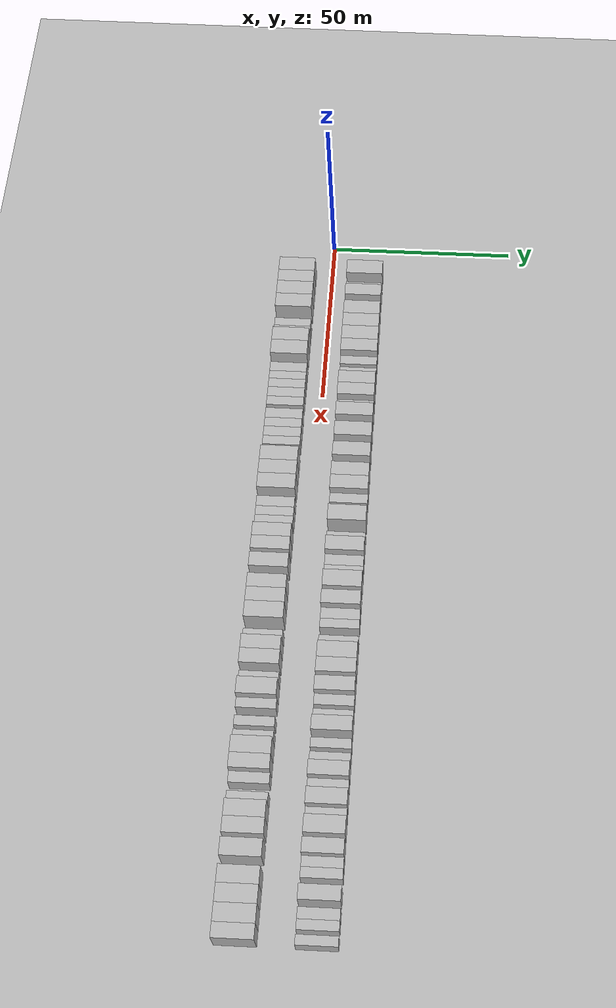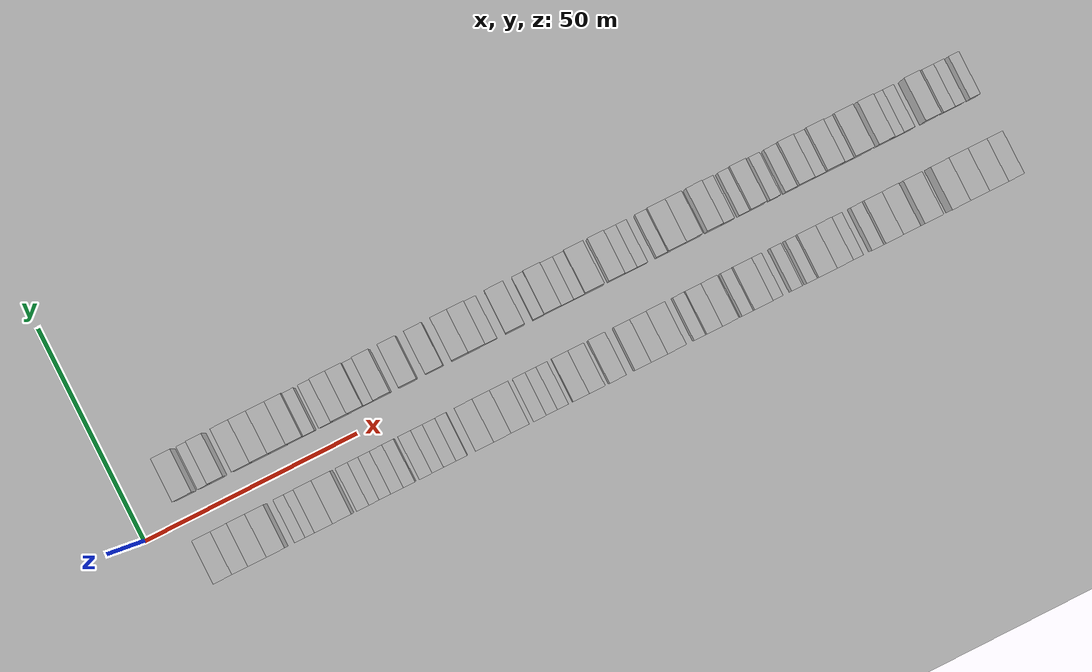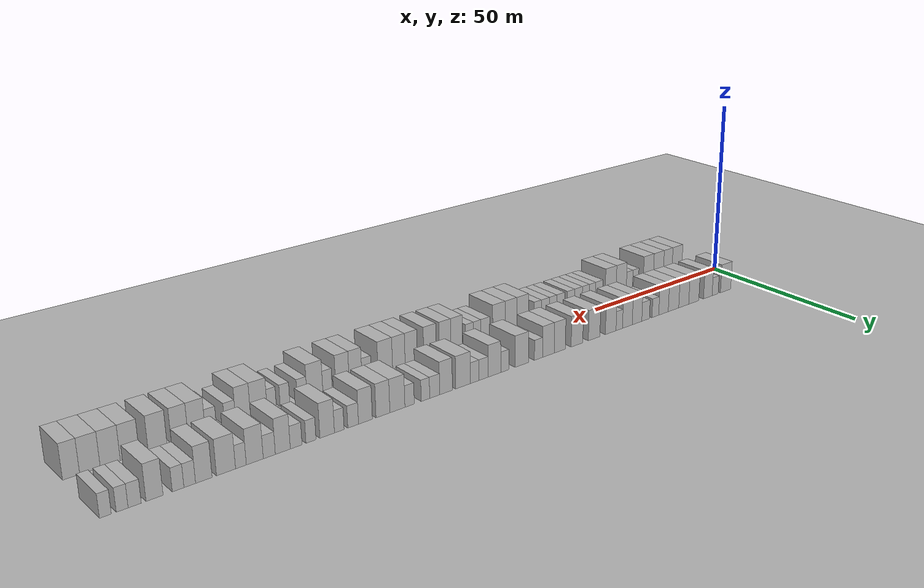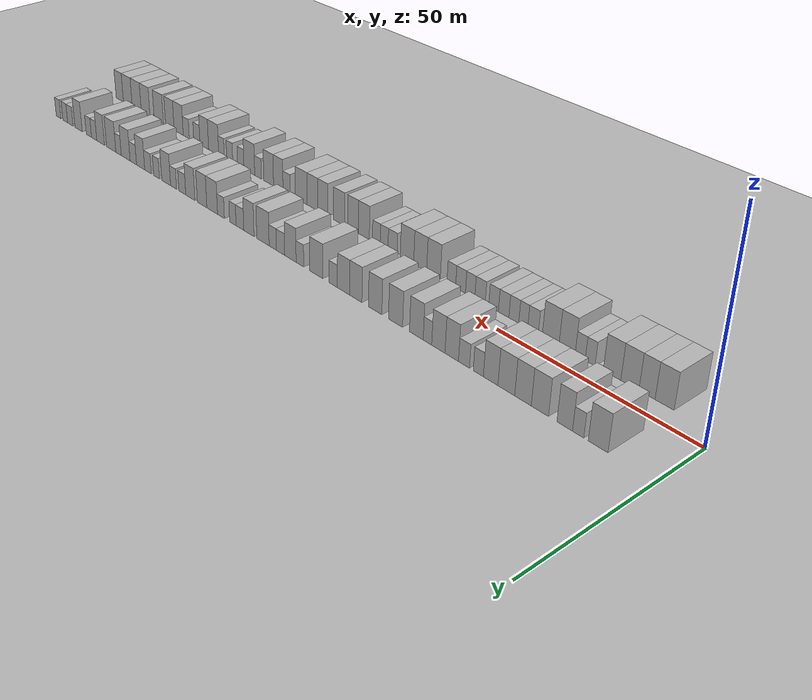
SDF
<?xml version="1.0" encoding="utf-8"?>

<sdf version="1.6">

   <world name="default">

      <gui fullscreen="0">

         <camera name="user_camera">

            <pose>-15 0 4.57585 0 0 0</pose>

            <view_controller>orbit</view_controller>

         </camera>

      </gui>

      <scene>

         <sky>

           <clouds>

             <speed>12</speed>

           </clouds>

         </sky>

         <ambient>0.4 0.4 0.4 1</ambient>

         <background>0.7 0.7 0.7 1</background>

         <shadows>1</shadows>

      </scene>

      <gravity>0 0 -9.8066</gravity>

      <magnetic_field>6e-06 2.3e-05 -4.2e-05</magnetic_field>

      <physics default="0" name="default_physics" type="ode">

         <ode>

            <solver>

               <type>quick</type>

               <iters>10</iters>

               <sor>1.0</sor>

               <use_dynamic_moi_rescaling>0</use_dynamic_moi_rescaling>

            </solver>

            <constraints>

               <cfm>0</cfm>

               <erp>0.2</erp>

               <contact_max_correcting_vel>100</contact_max_correcting_vel>

               <contact_surface_layer>0.001</contact_surface_layer>

            </constraints>

         </ode>

         <max_step_size>0.004</max_step_size>

         <real_time_factor>1</real_time_factor>

         <real_time_update_rate>250</real_time_update_rate>

      </physics>

      <light name="sun" type="directional">

         <cast_shadows>1</cast_shadows>

         <pose>0 0 10 0 0 0</pose>

         <diffuse>0.8 0.8 0.8 1</diffuse>

         <specular>0.2 0.2 0.2 1</specular>

         <attenuation>

            <range>1000</range>

            <constant>0.9</constant>

            <linear>0.01</linear>

            <quadratic>0.001</quadratic>

         </attenuation>

         <direction>-0.5 0.1 -0.9</direction>

      </light>

      <include>

         <name>ground_plane_1</name>

         <uri>model://HANNAS_ground_plane</uri>

         <pose>0 0 0  0 0 0</pose>

      </include>

      <include>

         <name>ground_plane_2</name>

         <uri>model://HANNAS_ground_plane</uri>

         <pose>100 0 0  0 0 0</pose>

      </include>

      <model name="building_1">

         <static>1</static>

         <pose frame="">12.2253 9.5000 0 0.000000 0.000000 1.570796</pose>

         <link name="link">

            <pose frame="">0 0 4.50 0 0 0</pose>

            <collision name="collision">

               <geometry>

                  <box>

                     <size>10.0000 4.4505 9.0000</size>

                  </box>

               </geometry>

               <max_contacts>10</max_contacts>

               <surface>

                  <contact>

                     <ode/>

                  </contact>

                  <bounce/>

                  <friction>

                     <torsional>

                        <ode/>

                     </torsional>

                     <ode/>

                  </friction>

               </surface>

            </collision>

            <visual name="visual">

               <cast_shadows>0</cast_shadows>

               <geometry>

                  <box>

                     <size>10.0000 4.4505 9.0000</size>

                  </box>

               </geometry>

               <material>

                  <script>

                     <uri>model://HANNAS_wall/materials/scripts</uri>

                     <uri>model://HANNAS_wall/materials/textures</uri>

                     <name>vrc/HANNAS_wall</name>

                  </script>

               </material>

            </visual>

            <self_collide>0</self_collide>

            <enable_wind>0</enable_wind>

            <kinematic>0</kinematic>

         </link>

      </model>

      <model name="building_2">

         <static>1</static>

         <pose frame="">16.7551 9.5000 0 0.000000 0.000000 1.570796</pose>

         <link name="link">

            <pose frame="">0 0 3.00 0 0 0</pose>

            <collision name="collision">

               <geometry>

                  <box>

                     <size>10.0000 2.6090 6.0000</size>

                  </box>

               </geometry>

               <max_contacts>10</max_contacts>

               <surface>

                  <contact>

                     <ode/>

                  </contact>

                  <bounce/>

                  <friction>

                     <torsional>

                        <ode/>

                     </torsional>

                     <ode/>

                  </friction>

               </surface>

            </collision>

            <visual name="visual">

               <cast_shadows>0</cast_shadows>

               <geometry>

                  <box>

                     <size>10.0000 2.6090 6.0000</size>

                  </box>

               </geometry>

               <material>

                  <script>

                     <uri>model://HANNAS_wall/materials/scripts</uri>

                     <uri>model://HANNAS_wall/materials/textures</uri>

                     <name>vrc/HANNAS_wall</name>

                  </script>

               </material>

            </visual>

            <self_collide>0</self_collide>

            <enable_wind>0</enable_wind>

            <kinematic>0</kinematic>

         </link>

      </model>

      <model name="building_3">

         <static>1</static>

         <pose frame="">19.8778 9.5000 0 0.000000 0.000000 1.570796</pose>

         <link name="link">

            <pose frame="">0 0 4.50 0 0 0</pose>

            <collision name="collision">

               <geometry>

                  <box>

                     <size>10.0000 3.6366 9.0000</size>

                  </box>

               </geometry>

               <max_contacts>10</max_contacts>

               <surface>

                  <contact>

                     <ode/>

                  </contact>

                  <bounce/>

                  <friction>

                     <torsional>

                        <ode/>

                     </torsional>

                     <ode/>

                  </friction>

               </surface>

            </collision>

            <visual name="visual">

               <cast_shadows>0</cast_shadows>

               <geometry>

                  <box>

                     <size>10.0000 3.6366 9.0000</size>

                  </box>

               </geometry>

               <material>

                  <script>

                     <uri>model://HANNAS_wall/materials/scripts</uri>

                     <uri>model://HANNAS_wall/materials/textures</uri>

                     <name>vrc/HANNAS_wall</name>

                  </script>

               </material>

            </visual>

            <self_collide>0</self_collide>

            <enable_wind>0</enable_wind>

            <kinematic>0</kinematic>

         </link>

      </model>

      <model name="building_4">

         <static>1</static>

         <pose frame="">25.7958 9.5000 0 0.000000 0.000000 1.570796</pose>

         <link name="link">

            <pose frame="">0 0 4.50 0 0 0</pose>

            <collision name="collision">

               <geometry>

                  <box>

                     <size>10.0000 4.1993 9.0000</size>

                  </box>

               </geometry>

               <max_contacts>10</max_contacts>

               <surface>

                  <contact>

                     <ode/>

                  </contact>

                  <bounce/>

                  <friction>

                     <torsional>

                        <ode/>

                     </torsional>

                     <ode/>

                  </friction>

               </surface>

            </collision>

            <visual name="visual">

               <cast_shadows>0</cast_shadows>

               <geometry>

                  <box>

                     <size>10.0000 4.1993 9.0000</size>

                  </box>

               </geometry>

               <material>

                  <script>

                     <uri>model://HANNAS_wall/materials/scripts</uri>

                     <uri>model://HANNAS_wall/materials/textures</uri>

                     <name>vrc/HANNAS_wall</name>

                  </script>

               </material>

            </visual>

            <self_collide>0</self_collide>

            <enable_wind>0</enable_wind>

            <kinematic>0</kinematic>

         </link>

      </model>

      <model name="building_5">

         <static>1</static>

         <pose frame="">29.9410 9.5000 0 0.000000 0.000000 1.570796</pose>

         <link name="link">

            <pose frame="">0 0 4.50 0 0 0</pose>

            <collision name="collision">

               <geometry>

                  <box>

                     <size>10.0000 4.0912 9.0000</size>

                  </box>

               </geometry>

               <max_contacts>10</max_contacts>

               <surface>

                  <contact>

                     <ode/>

                  </contact>

                  <bounce/>

                  <friction>

                     <torsional>

                        <ode/>

                     </torsional>

                     <ode/>

                  </friction>

               </surface>

            </collision>

            <visual name="visual">

               <cast_shadows>0</cast_shadows>

               <geometry>

                  <box>

                     <size>10.0000 4.0912 9.0000</size>

                  </box>

               </geometry>

               <material>

                  <script>

                     <uri>model://HANNAS_wall/materials/scripts</uri>

                     <uri>model://HANNAS_wall/materials/textures</uri>

                     <name>vrc/HANNAS_wall</name>

                  </script>

               </material>

            </visual>

            <self_collide>0</self_collide>

            <enable_wind>0</enable_wind>

            <kinematic>0</kinematic>

         </link>

      </model>

      <model name="building_6">

         <static>1</static>

         <pose frame="">34.1102 9.5000 0 0.000000 0.000000 1.570796</pose>

         <link name="link">

            <pose frame="">0 0 4.50 0 0 0</pose>

            <collision name="collision">

               <geometry>

                  <box>

                     <size>10.0000 4.2470 9.0000</size>

                  </box>

               </geometry>

               <max_contacts>10</max_contacts>

               <surface>

                  <contact>

                     <ode/>

                  </contact>

                  <bounce/>

                  <friction>

                     <torsional>

                        <ode/>

                     </torsional>

                     <ode/>

                  </friction>

               </surface>

            </collision>

            <visual name="visual">

               <cast_shadows>0</cast_shadows>

               <geometry>

                  <box>

                     <size>10.0000 4.2470 9.0000</size>

                  </box>

               </geometry>

               <material>

                  <script>

                     <uri>model://HANNAS_wall/materials/scripts</uri>

                     <uri>model://HANNAS_wall/materials/textures</uri>

                     <name>vrc/HANNAS_wall</name>

                  </script>

               </material>

            </visual>

            <self_collide>0</self_collide>

            <enable_wind>0</enable_wind>

            <kinematic>0</kinematic>

         </link>

      </model>

      <model name="building_7">

         <static>1</static>

         <pose frame="">38.1271 9.5000 0 0.000000 0.000000 1.570796</pose>

         <link name="link">

            <pose frame="">0 0 4.50 0 0 0</pose>

            <collision name="collision">

               <geometry>

                  <box>

                     <size>10.0000 3.7868 9.0000</size>

                  </box>

               </geometry>

               <max_contacts>10</max_contacts>

               <surface>

                  <contact>

                     <ode/>

                  </contact>

                  <bounce/>

                  <friction>

                     <torsional>

                        <ode/>

                     </torsional>

                     <ode/>

                  </friction>

               </surface>

            </collision>

            <visual name="visual">

               <cast_shadows>0</cast_shadows>

               <geometry>

                  <box>

                     <size>10.0000 3.7868 9.0000</size>

                  </box>

               </geometry>

               <material>

                  <script>

                     <uri>model://HANNAS_wall/materials/scripts</uri>

                     <uri>model://HANNAS_wall/materials/textures</uri>

                     <name>vrc/HANNAS_wall</name>

                  </script>

               </material>

            </visual>

            <self_collide>0</self_collide>

            <enable_wind>0</enable_wind>

            <kinematic>0</kinematic>

         </link>

      </model>

      <model name="building_8">

         <static>1</static>

         <pose frame="">41.3472 9.5000 0 0.000000 0.000000 1.570796</pose>

         <link name="link">

            <pose frame="">0 0 3.00 0 0 0</pose>

            <collision name="collision">

               <geometry>

                  <box>

                     <size>10.0000 2.6535 6.0000</size>

                  </box>

               </geometry>

               <max_contacts>10</max_contacts>

               <surface>

                  <contact>

                     <ode/>

                  </contact>

                  <bounce/>

                  <friction>

                     <torsional>

                        <ode/>

                     </torsional>

                     <ode/>

                  </friction>

               </surface>

            </collision>

            <visual name="visual">

               <cast_shadows>0</cast_shadows>

               <geometry>

                  <box>

                     <size>10.0000 2.6535 6.0000</size>

                  </box>

               </geometry>

               <material>

                  <script>

                     <uri>model://HANNAS_wall/materials/scripts</uri>

                     <uri>model://HANNAS_wall/materials/textures</uri>

                     <name>vrc/HANNAS_wall</name>

                  </script>

               </material>

            </visual>

            <self_collide>0</self_collide>

            <enable_wind>0</enable_wind>

            <kinematic>0</kinematic>

         </link>

      </model>

      <model name="building_9">

         <static>1</static>

         <pose frame="">45.1567 9.5000 0 0.000000 0.000000 1.570796</pose>

         <link name="link">

            <pose frame="">0 0 3.00 0 0 0</pose>

            <collision name="collision">

               <geometry>

                  <box>

                     <size>10.0000 2.9655 6.0000</size>

                  </box>

               </geometry>

               <max_contacts>10</max_contacts>

               <surface>

                  <contact>

                     <ode/>

                  </contact>

                  <bounce/>

                  <friction>

                     <torsional>

                        <ode/>

                     </torsional>

                     <ode/>

                  </friction>

               </surface>

            </collision>

            <visual name="visual">

               <cast_shadows>0</cast_shadows>

               <geometry>

                  <box>

                     <size>10.0000 2.9655 6.0000</size>

                  </box>

               </geometry>

               <material>

                  <script>

                     <uri>model://HANNAS_wall/materials/scripts</uri>

                     <uri>model://HANNAS_wall/materials/textures</uri>

                     <name>vrc/HANNAS_wall</name>

                  </script>

               </material>

            </visual>

            <self_collide>0</self_collide>

            <enable_wind>0</enable_wind>

            <kinematic>0</kinematic>

         </link>

      </model>

      <model name="building_10">

         <static>1</static>

         <pose frame="">48.4828 9.5000 0 0.000000 0.000000 1.570796</pose>

         <link name="link">

            <pose frame="">0 0 4.50 0 0 0</pose>

            <collision name="collision">

               <geometry>

                  <box>

                     <size>10.0000 3.6868 9.0000</size>

                  </box>

               </geometry>

               <max_contacts>10</max_contacts>

               <surface>

                  <contact>

                     <ode/>

                  </contact>

                  <bounce/>

                  <friction>

                     <torsional>

                        <ode/>

                     </torsional>

                     <ode/>

                  </friction>

               </surface>

            </collision>

            <visual name="visual">

               <cast_shadows>0</cast_shadows>

               <geometry>

                  <box>

                     <size>10.0000 3.6868 9.0000</size>

                  </box>

               </geometry>

               <material>

                  <script>

                     <uri>model://HANNAS_wall/materials/scripts</uri>

                     <uri>model://HANNAS_wall/materials/textures</uri>

                     <name>vrc/HANNAS_wall</name>

                  </script>

               </material>

            </visual>

            <self_collide>0</self_collide>

            <enable_wind>0</enable_wind>

            <kinematic>0</kinematic>

         </link>

      </model>

      <model name="building_11">

         <static>1</static>

         <pose frame="">52.1772 9.5000 0 0.000000 0.000000 1.570796</pose>

         <link name="link">

            <pose frame="">0 0 4.50 0 0 0</pose>

            <collision name="collision">

               <geometry>

                  <box>

                     <size>10.0000 3.7020 9.0000</size>

                  </box>

               </geometry>

               <max_contacts>10</max_contacts>

               <surface>

                  <contact>

                     <ode/>

                  </contact>

                  <bounce/>

                  <friction>

                     <torsional>

                        <ode/>

                     </torsional>

                     <ode/>

                  </friction>

               </surface>

            </collision>

            <visual name="visual">

               <cast_shadows>0</cast_shadows>

               <geometry>

                  <box>

                     <size>10.0000 3.7020 9.0000</size>

                  </box>

               </geometry>

               <material>

                  <script>

                     <uri>model://HANNAS_wall/materials/scripts</uri>

                     <uri>model://HANNAS_wall/materials/textures</uri>

                     <name>vrc/HANNAS_wall</name>

                  </script>

               </material>

            </visual>

            <self_collide>0</self_collide>

            <enable_wind>0</enable_wind>

            <kinematic>0</kinematic>

         </link>

      </model>

      <model name="building_12">

         <static>1</static>

         <pose frame="">55.2314 9.5000 0 0.000000 0.000000 1.570796</pose>

         <link name="link">

            <pose frame="">0 0 3.00 0 0 0</pose>

            <collision name="collision">

               <geometry>

                  <box>

                     <size>10.0000 2.4064 6.0000</size>

                  </box>

               </geometry>

               <max_contacts>10</max_contacts>

               <surface>

                  <contact>

                     <ode/>

                  </contact>

                  <bounce/>

                  <friction>

                     <torsional>

                        <ode/>

                     </torsional>

                     <ode/>

                  </friction>

               </surface>

            </collision>

            <visual name="visual">

               <cast_shadows>0</cast_shadows>

               <geometry>

                  <box>

                     <size>10.0000 2.4064 6.0000</size>

                  </box>

               </geometry>

               <material>

                  <script>

                     <uri>model://HANNAS_wall/materials/scripts</uri>

                     <uri>model://HANNAS_wall/materials/textures</uri>

                     <name>vrc/HANNAS_wall</name>

                  </script>

               </material>

            </visual>

            <self_collide>0</self_collide>

            <enable_wind>0</enable_wind>

            <kinematic>0</kinematic>

         </link>

      </model>

      <model name="building_13">

         <static>1</static>

         <pose frame="">58.4080 9.5000 0 0.000000 0.000000 1.570796</pose>

         <link name="link">

            <pose frame="">0 0 4.50 0 0 0</pose>

            <collision name="collision">

               <geometry>

                  <box>

                     <size>10.0000 3.9468 9.0000</size>

                  </box>

               </geometry>

               <max_contacts>10</max_contacts>

               <surface>

                  <contact>

                     <ode/>

                  </contact>

                  <bounce/>

                  <friction>

                     <torsional>

                        <ode/>

                     </torsional>

                     <ode/>

                  </friction>

               </surface>

            </collision>

            <visual name="visual">

               <cast_shadows>0</cast_shadows>

               <geometry>

                  <box>

                     <size>10.0000 3.9468 9.0000</size>

                  </box>

               </geometry>

               <material>

                  <script>

                     <uri>model://HANNAS_wall/materials/scripts</uri>

                     <uri>model://HANNAS_wall/materials/textures</uri>

                     <name>vrc/HANNAS_wall</name>

                  </script>

               </material>

            </visual>

            <self_collide>0</self_collide>

            <enable_wind>0</enable_wind>

            <kinematic>0</kinematic>

         </link>

      </model>

      <model name="building_14">

         <static>1</static>

         <pose frame="">64.4760 9.5000 0 0.000000 0.000000 1.570796</pose>

         <link name="link">

            <pose frame="">0 0 4.50 0 0 0</pose>

            <collision name="collision">

               <geometry>

                  <box>

                     <size>10.0000 4.1894 9.0000</size>

                  </box>

               </geometry>

               <max_contacts>10</max_contacts>

               <surface>

                  <contact>

                     <ode/>

                  </contact>

                  <bounce/>

                  <friction>

                     <torsional>

                        <ode/>

                     </torsional>

                     <ode/>

                  </friction>

               </surface>

            </collision>

            <visual name="visual">

               <cast_shadows>0</cast_shadows>

               <geometry>

                  <box>

                     <size>10.0000 4.1894 9.0000</size>

                  </box>

               </geometry>

               <material>

                  <script>

                     <uri>model://HANNAS_wall/materials/scripts</uri>

                     <uri>model://HANNAS_wall/materials/textures</uri>

                     <name>vrc/HANNAS_wall</name>

                  </script>

               </material>

            </visual>

            <self_collide>0</self_collide>

            <enable_wind>0</enable_wind>

            <kinematic>0</kinematic>

         </link>

      </model>

      <model name="building_15">

         <static>1</static>

         <pose frame="">70.6249 9.5000 0 0.000000 0.000000 1.570796</pose>

         <link name="link">

            <pose frame="">0 0 4.50 0 0 0</pose>

            <collision name="collision">

               <geometry>

                  <box>

                     <size>10.0000 4.1084 9.0000</size>

                  </box>

               </geometry>

               <max_contacts>10</max_contacts>

               <surface>

                  <contact>

                     <ode/>

                  </contact>

                  <bounce/>

                  <friction>

                     <torsional>

                        <ode/>

                     </torsional>

                     <ode/>

                  </friction>

               </surface>

            </collision>

            <visual name="visual">

               <cast_shadows>0</cast_shadows>

               <geometry>

                  <box>

                     <size>10.0000 4.1084 9.0000</size>

                  </box>

               </geometry>

               <material>

                  <script>

                     <uri>model://HANNAS_wall/materials/scripts</uri>

                     <uri>model://HANNAS_wall/materials/textures</uri>

                     <name>vrc/HANNAS_wall</name>

                  </script>

               </material>

            </visual>

            <self_collide>0</self_collide>

            <enable_wind>0</enable_wind>

            <kinematic>0</kinematic>

         </link>

      </model>

      <model name="building_16">

         <static>1</static>

         <pose frame="">76.6227 9.5000 0 0.000000 0.000000 1.570796</pose>

         <link name="link">

            <pose frame="">0 0 4.50 0 0 0</pose>

            <collision name="collision">

               <geometry>

                  <box>

                     <size>10.0000 3.8872 9.0000</size>

                  </box>

               </geometry>

               <max_contacts>10</max_contacts>

               <surface>

                  <contact>

                     <ode/>

                  </contact>

                  <bounce/>

                  <friction>

                     <torsional>

                        <ode/>

                     </torsional>

                     <ode/>

                  </friction>

               </surface>

            </collision>

            <visual name="visual">

               <cast_shadows>0</cast_shadows>

               <geometry>

                  <box>

                     <size>10.0000 3.8872 9.0000</size>

                  </box>

               </geometry>

               <material>

                  <script>

                     <uri>model://HANNAS_wall/materials/scripts</uri>

                     <uri>model://HANNAS_wall/materials/textures</uri>

                     <name>vrc/HANNAS_wall</name>

                  </script>

               </material>

            </visual>

            <self_collide>0</self_collide>

            <enable_wind>0</enable_wind>

            <kinematic>0</kinematic>

         </link>

      </model>

      <model name="building_17">

         <static>1</static>

         <pose frame="">80.5345 9.5000 0 0.000000 0.000000 1.570796</pose>

         <link name="link">

            <pose frame="">0 0 4.50 0 0 0</pose>

            <collision name="collision">

               <geometry>

                  <box>

                     <size>10.0000 3.9363 9.0000</size>

                  </box>

               </geometry>

               <max_contacts>10</max_contacts>

               <surface>

                  <contact>

                     <ode/>

                  </contact>

                  <bounce/>

                  <friction>

                     <torsional>

                        <ode/>

                     </torsional>

                     <ode/>

                  </friction>

               </surface>

            </collision>

            <visual name="visual">

               <cast_shadows>0</cast_shadows>

               <geometry>

                  <box>

                     <size>10.0000 3.9363 9.0000</size>

                  </box>

               </geometry>

               <material>

                  <script>

                     <uri>model://HANNAS_wall/materials/scripts</uri>

                     <uri>model://HANNAS_wall/materials/textures</uri>

                     <name>vrc/HANNAS_wall</name>

                  </script>

               </material>

            </visual>

            <self_collide>0</self_collide>

            <enable_wind>0</enable_wind>

            <kinematic>0</kinematic>

         </link>

      </model>

      <model name="building_18">

         <static>1</static>

         <pose frame="">83.8869 9.5000 0 0.000000 0.000000 1.570796</pose>

         <link name="link">

            <pose frame="">0 0 3.00 0 0 0</pose>

            <collision name="collision">

               <geometry>

                  <box>

                     <size>10.0000 2.7687 6.0000</size>

                  </box>

               </geometry>

               <max_contacts>10</max_contacts>

               <surface>

                  <contact>

                     <ode/>

                  </contact>

                  <bounce/>

                  <friction>

                     <torsional>

                        <ode/>

                     </torsional>

                     <ode/>

                  </friction>

               </surface>

            </collision>

            <visual name="visual">

               <cast_shadows>0</cast_shadows>

               <geometry>

                  <box>

                     <size>10.0000 2.7687 6.0000</size>

                  </box>

               </geometry>

               <material>

                  <script>

                     <uri>model://HANNAS_wall/materials/scripts</uri>

                     <uri>model://HANNAS_wall/materials/textures</uri>

                     <name>vrc/HANNAS_wall</name>

                  </script>

               </material>

            </visual>

            <self_collide>0</self_collide>

            <enable_wind>0</enable_wind>

            <kinematic>0</kinematic>

         </link>

      </model>

      <model name="building_19">

         <static>1</static>

         <pose frame="">89.4731 9.5000 0 0.000000 0.000000 1.570796</pose>

         <link name="link">

            <pose frame="">0 0 4.50 0 0 0</pose>

            <collision name="collision">

               <geometry>

                  <box>

                     <size>10.0000 4.4036 9.0000</size>

                  </box>

               </geometry>

               <max_contacts>10</max_contacts>

               <surface>

                  <contact>

                     <ode/>

                  </contact>

                  <bounce/>

                  <friction>

                     <torsional>

                        <ode/>

                     </torsional>

                     <ode/>

                  </friction>

               </surface>

            </collision>

            <visual name="visual">

               <cast_shadows>0</cast_shadows>

               <geometry>

                  <box>

                     <size>10.0000 4.4036 9.0000</size>

                  </box>

               </geometry>

               <material>

                  <script>

                     <uri>model://HANNAS_wall/materials/scripts</uri>

                     <uri>model://HANNAS_wall/materials/textures</uri>

                     <name>vrc/HANNAS_wall</name>

                  </script>

               </material>

            </visual>

            <self_collide>0</self_collide>

            <enable_wind>0</enable_wind>

            <kinematic>0</kinematic>

         </link>

      </model>

      <model name="building_20">

         <static>1</static>

         <pose frame="">94.9758 9.5000 0 0.000000 0.000000 1.570796</pose>

         <link name="link">

            <pose frame="">0 0 3.00 0 0 0</pose>

            <collision name="collision">

               <geometry>

                  <box>

                     <size>10.0000 2.6017 6.0000</size>

                  </box>

               </geometry>

               <max_contacts>10</max_contacts>

               <surface>

                  <contact>

                     <ode/>

                  </contact>

                  <bounce/>

                  <friction>

                     <torsional>

                        <ode/>

                     </torsional>

                     <ode/>

                  </friction>

               </surface>

            </collision>

            <visual name="visual">

               <cast_shadows>0</cast_shadows>

               <geometry>

                  <box>

                     <size>10.0000 2.6017 6.0000</size>

                  </box>

               </geometry>

               <material>

                  <script>

                     <uri>model://HANNAS_wall/materials/scripts</uri>

                     <uri>model://HANNAS_wall/materials/textures</uri>

                     <name>vrc/HANNAS_wall</name>

                  </script>

               </material>

            </visual>

            <self_collide>0</self_collide>

            <enable_wind>0</enable_wind>

            <kinematic>0</kinematic>

         </link>

      </model>

      <model name="building_21">

         <static>1</static>

         <pose frame="">98.2607 9.5000 0 0.000000 0.000000 1.570796</pose>

         <link name="link">

            <pose frame="">0 0 4.50 0 0 0</pose>

            <collision name="collision">

               <geometry>

                  <box>

                     <size>10.0000 3.9682 9.0000</size>

                  </box>

               </geometry>

               <max_contacts>10</max_contacts>

               <surface>

                  <contact>

                     <ode/>

                  </contact>

                  <bounce/>

                  <friction>

                     <torsional>

                        <ode/>

                     </torsional>

                     <ode/>

                  </friction>

               </surface>

            </collision>

            <visual name="visual">

               <cast_shadows>0</cast_shadows>

               <geometry>

                  <box>

                     <size>10.0000 3.9682 9.0000</size>

                  </box>

               </geometry>

               <material>

                  <script>

                     <uri>model://HANNAS_wall/materials/scripts</uri>

                     <uri>model://HANNAS_wall/materials/textures</uri>

                     <name>vrc/HANNAS_wall</name>

                  </script>

               </material>

            </visual>

            <self_collide>0</self_collide>

            <enable_wind>0</enable_wind>

            <kinematic>0</kinematic>

         </link>

      </model>

      <model name="building_22">

         <static>1</static>

         <pose frame="">101.7317 9.5000 0 0.000000 0.000000 1.570796</pose>

         <link name="link">

            <pose frame="">0 0 3.00 0 0 0</pose>

            <collision name="collision">

               <geometry>

                  <box>

                     <size>10.0000 2.9739 6.0000</size>

                  </box>

               </geometry>

               <max_contacts>10</max_contacts>

               <surface>

                  <contact>

                     <ode/>

                  </contact>

                  <bounce/>

                  <friction>

                     <torsional>

                        <ode/>

                     </torsional>

                     <ode/>

                  </friction>

               </surface>

            </collision>

            <visual name="visual">

               <cast_shadows>0</cast_shadows>

               <geometry>

                  <box>

                     <size>10.0000 2.9739 6.0000</size>

                  </box>

               </geometry>

               <material>

                  <script>

                     <uri>model://HANNAS_wall/materials/scripts</uri>

                     <uri>model://HANNAS_wall/materials/textures</uri>

                     <name>vrc/HANNAS_wall</name>

                  </script>

               </material>

            </visual>

            <self_collide>0</self_collide>

            <enable_wind>0</enable_wind>

            <kinematic>0</kinematic>

         </link>

      </model>

      <model name="building_23">

         <static>1</static>

         <pose frame="">104.5063 9.5000 0 0.000000 0.000000 1.570796</pose>

         <link name="link">

            <pose frame="">0 0 3.00 0 0 0</pose>

            <collision name="collision">

               <geometry>

                  <box>

                     <size>10.0000 2.5752 6.0000</size>

                  </box>

               </geometry>

               <max_contacts>10</max_contacts>

               <surface>

                  <contact>

                     <ode/>

                  </contact>

                  <bounce/>

                  <friction>

                     <torsional>

                        <ode/>

                     </torsional>

                     <ode/>

                  </friction>

               </surface>

            </collision>

            <visual name="visual">

               <cast_shadows>0</cast_shadows>

               <geometry>

                  <box>

                     <size>10.0000 2.5752 6.0000</size>

                  </box>

               </geometry>

               <material>

                  <script>

                     <uri>model://HANNAS_wall/materials/scripts</uri>

                     <uri>model://HANNAS_wall/materials/textures</uri>

                     <name>vrc/HANNAS_wall</name>

                  </script>

               </material>

            </visual>

            <self_collide>0</self_collide>

            <enable_wind>0</enable_wind>

            <kinematic>0</kinematic>

         </link>

      </model>

      <model name="building_24">

         <static>1</static>

         <pose frame="">108.0437 9.5000 0 0.000000 0.000000 1.570796</pose>

         <link name="link">

            <pose frame="">0 0 4.50 0 0 0</pose>

            <collision name="collision">

               <geometry>

                  <box>

                     <size>10.0000 4.4995 9.0000</size>

                  </box>

               </geometry>

               <max_contacts>10</max_contacts>

               <surface>

                  <contact>

                     <ode/>

                  </contact>

                  <bounce/>

                  <friction>

                     <torsional>

                        <ode/>

                     </torsional>

                     <ode/>

                  </friction>

               </surface>

            </collision>

            <visual name="visual">

               <cast_shadows>0</cast_shadows>

               <geometry>

                  <box>

                     <size>10.0000 4.4995 9.0000</size>

                  </box>

               </geometry>

               <material>

                  <script>

                     <uri>model://HANNAS_wall/materials/scripts</uri>

                     <uri>model://HANNAS_wall/materials/textures</uri>

                     <name>vrc/HANNAS_wall</name>

                  </script>

               </material>

            </visual>

            <self_collide>0</self_collide>

            <enable_wind>0</enable_wind>

            <kinematic>0</kinematic>

         </link>

      </model>

      <model name="building_25">

         <static>1</static>

         <pose frame="">113.1949 9.5000 0 0.000000 0.000000 1.570796</pose>

         <link name="link">

            <pose frame="">0 0 4.50 0 0 0</pose>

            <collision name="collision">

               <geometry>

                  <box>

                     <size>10.0000 3.8029 9.0000</size>

                  </box>

               </geometry>

               <max_contacts>10</max_contacts>

               <surface>

                  <contact>

                     <ode/>

                  </contact>

                  <bounce/>

                  <friction>

                     <torsional>

                        <ode/>

                     </torsional>

                     <ode/>

                  </friction>

               </surface>

            </collision>

            <visual name="visual">

               <cast_shadows>0</cast_shadows>

               <geometry>

                  <box>

                     <size>10.0000 3.8029 9.0000</size>

                  </box>

               </geometry>

               <material>

                  <script>

                     <uri>model://HANNAS_wall/materials/scripts</uri>

                     <uri>model://HANNAS_wall/materials/textures</uri>

                     <name>vrc/HANNAS_wall</name>

                  </script>

               </material>

            </visual>

            <self_collide>0</self_collide>

            <enable_wind>0</enable_wind>

            <kinematic>0</kinematic>

         </link>

      </model>

      <model name="building_26">

         <static>1</static>

         <pose frame="">116.5691 9.5000 0 0.000000 0.000000 1.570796</pose>

         <link name="link">

            <pose frame="">0 0 3.00 0 0 0</pose>

            <collision name="collision">

               <geometry>

                  <box>

                     <size>10.0000 2.9457 6.0000</size>

                  </box>

               </geometry>

               <max_contacts>10</max_contacts>

               <surface>

                  <contact>

                     <ode/>

                  </contact>

                  <bounce/>

                  <friction>

                     <torsional>

                        <ode/>

                     </torsional>

                     <ode/>

                  </friction>

               </surface>

            </collision>

            <visual name="visual">

               <cast_shadows>0</cast_shadows>

               <geometry>

                  <box>

                     <size>10.0000 2.9457 6.0000</size>

                  </box>

               </geometry>

               <material>

                  <script>

                     <uri>model://HANNAS_wall/materials/scripts</uri>

                     <uri>model://HANNAS_wall/materials/textures</uri>

                     <name>vrc/HANNAS_wall</name>

                  </script>

               </material>

            </visual>

            <self_collide>0</self_collide>

            <enable_wind>0</enable_wind>

            <kinematic>0</kinematic>

         </link>

      </model>

      <model name="building_27">

         <static>1</static>

         <pose frame="">119.2796 9.5000 0 0.000000 0.000000 1.570796</pose>

         <link name="link">

            <pose frame="">0 0 3.00 0 0 0</pose>

            <collision name="collision">

               <geometry>

                  <box>

                     <size>10.0000 2.4752 6.0000</size>

                  </box>

               </geometry>

               <max_contacts>10</max_contacts>

               <surface>

                  <contact>

                     <ode/>

                  </contact>

                  <bounce/>

                  <friction>

                     <torsional>

                        <ode/>

                     </torsional>

                     <ode/>

                  </friction>

               </surface>

            </collision>

            <visual name="visual">

               <cast_shadows>0</cast_shadows>

               <geometry>

                  <box>

                     <size>10.0000 2.4752 6.0000</size>

                  </box>

               </geometry>

               <material>

                  <script>

                     <uri>model://HANNAS_wall/materials/scripts</uri>

                     <uri>model://HANNAS_wall/materials/textures</uri>

                     <name>vrc/HANNAS_wall</name>

                  </script>

               </material>

            </visual>

            <self_collide>0</self_collide>

            <enable_wind>0</enable_wind>

            <kinematic>0</kinematic>

         </link>

      </model>

      <model name="building_28">

         <static>1</static>

         <pose frame="">123.8556 9.5000 0 0.000000 0.000000 1.570796</pose>

         <link name="link">

            <pose frame="">0 0 3.00 0 0 0</pose>

            <collision name="collision">

               <geometry>

                  <box>

                     <size>10.0000 2.6768 6.0000</size>

                  </box>

               </geometry>

               <max_contacts>10</max_contacts>

               <surface>

                  <contact>

                     <ode/>

                  </contact>

                  <bounce/>

                  <friction>

                     <torsional>

                        <ode/>

                     </torsional>

                     <ode/>

                  </friction>

               </surface>

            </collision>

            <visual name="visual">

               <cast_shadows>0</cast_shadows>

               <geometry>

                  <box>

                     <size>10.0000 2.6768 6.0000</size>

                  </box>

               </geometry>

               <material>

                  <script>

                     <uri>model://HANNAS_wall/materials/scripts</uri>

                     <uri>model://HANNAS_wall/materials/textures</uri>

                     <name>vrc/HANNAS_wall</name>

                  </script>

               </material>

            </visual>

            <self_collide>0</self_collide>

            <enable_wind>0</enable_wind>

            <kinematic>0</kinematic>

         </link>

      </model>

      <model name="building_29">

         <static>1</static>

         <pose frame="">127.3138 9.5000 0 0.000000 0.000000 1.570796</pose>

         <link name="link">

            <pose frame="">0 0 4.50 0 0 0</pose>

            <collision name="collision">

               <geometry>

                  <box>

                     <size>10.0000 4.2395 9.0000</size>

                  </box>

               </geometry>

               <max_contacts>10</max_contacts>

               <surface>

                  <contact>

                     <ode/>

                  </contact>

                  <bounce/>

                  <friction>

                     <torsional>

                        <ode/>

                     </torsional>

                     <ode/>

                  </friction>

               </surface>

            </collision>

            <visual name="visual">

               <cast_shadows>0</cast_shadows>

               <geometry>

                  <box>

                     <size>10.0000 4.2395 9.0000</size>

                  </box>

               </geometry>

               <material>

                  <script>

                     <uri>model://HANNAS_wall/materials/scripts</uri>

                     <uri>model://HANNAS_wall/materials/textures</uri>

                     <name>vrc/HANNAS_wall</name>

                  </script>

               </material>

            </visual>

            <self_collide>0</self_collide>

            <enable_wind>0</enable_wind>

            <kinematic>0</kinematic>

         </link>

      </model>

      <model name="building_30">

         <static>1</static>

         <pose frame="">131.3502 9.5000 0 0.000000 0.000000 1.570796</pose>

         <link name="link">

            <pose frame="">0 0 4.50 0 0 0</pose>

            <collision name="collision">

               <geometry>

                  <box>

                     <size>10.0000 3.8334 9.0000</size>

                  </box>

               </geometry>

               <max_contacts>10</max_contacts>

               <surface>

                  <contact>

                     <ode/>

                  </contact>

                  <bounce/>

                  <friction>

                     <torsional>

                        <ode/>

                     </torsional>

                     <ode/>

                  </friction>

               </surface>

            </collision>

            <visual name="visual">

               <cast_shadows>0</cast_shadows>

               <geometry>

                  <box>

                     <size>10.0000 3.8334 9.0000</size>

                  </box>

               </geometry>

               <material>

                  <script>

                     <uri>model://HANNAS_wall/materials/scripts</uri>

                     <uri>model://HANNAS_wall/materials/textures</uri>

                     <name>vrc/HANNAS_wall</name>

                  </script>

               </material>

            </visual>

            <self_collide>0</self_collide>

            <enable_wind>0</enable_wind>

            <kinematic>0</kinematic>

         </link>

      </model>

      <model name="building_31">

         <static>1</static>

         <pose frame="">136.1513 9.5000 0 0.000000 0.000000 1.570796</pose>

         <link name="link">

            <pose frame="">0 0 4.50 0 0 0</pose>

            <collision name="collision">

               <geometry>

                  <box>

                     <size>10.0000 3.7687 9.0000</size>

                  </box>

               </geometry>

               <max_contacts>10</max_contacts>

               <surface>

                  <contact>

                     <ode/>

                  </contact>

                  <bounce/>

                  <friction>

                     <torsional>

                        <ode/>

                     </torsional>

                     <ode/>

                  </friction>

               </surface>

            </collision>

            <visual name="visual">

               <cast_shadows>0</cast_shadows>

               <geometry>

                  <box>

                     <size>10.0000 3.7687 9.0000</size>

                  </box>

               </geometry>

               <material>

                  <script>

                     <uri>model://HANNAS_wall/materials/scripts</uri>

                     <uri>model://HANNAS_wall/materials/textures</uri>

                     <name>vrc/HANNAS_wall</name>

                  </script>

               </material>

            </visual>

            <self_collide>0</self_collide>

            <enable_wind>0</enable_wind>

            <kinematic>0</kinematic>

         </link>

      </model>

      <model name="building_32">

         <static>1</static>

         <pose frame="">139.4616 9.5000 0 0.000000 0.000000 1.570796</pose>

         <link name="link">

            <pose frame="">0 0 3.00 0 0 0</pose>

            <collision name="collision">

               <geometry>

                  <box>

                     <size>10.0000 2.8519 6.0000</size>

                  </box>

               </geometry>

               <max_contacts>10</max_contacts>

               <surface>

                  <contact>

                     <ode/>

                  </contact>

                  <bounce/>

                  <friction>

                     <torsional>

                        <ode/>

                     </torsional>

                     <ode/>

                  </friction>

               </surface>

            </collision>

            <visual name="visual">

               <cast_shadows>0</cast_shadows>

               <geometry>

                  <box>

                     <size>10.0000 2.8519 6.0000</size>

                  </box>

               </geometry>

               <material>

                  <script>

                     <uri>model://HANNAS_wall/materials/scripts</uri>

                     <uri>model://HANNAS_wall/materials/textures</uri>

                     <name>vrc/HANNAS_wall</name>

                  </script>

               </material>

            </visual>

            <self_collide>0</self_collide>

            <enable_wind>0</enable_wind>

            <kinematic>0</kinematic>

         </link>

      </model>

      <model name="building_33">

         <static>1</static>

         <pose frame="">143.1523 9.5000 0 0.000000 0.000000 1.570796</pose>

         <link name="link">

            <pose frame="">0 0 3.00 0 0 0</pose>

            <collision name="collision">

               <geometry>

                  <box>

                     <size>10.0000 2.5296 6.0000</size>

                  </box>

               </geometry>

               <max_contacts>10</max_contacts>

               <surface>

                  <contact>

                     <ode/>

                  </contact>

                  <bounce/>

                  <friction>

                     <torsional>

                        <ode/>

                     </torsional>

                     <ode/>

                  </friction>

               </surface>

            </collision>

            <visual name="visual">

               <cast_shadows>0</cast_shadows>

               <geometry>

                  <box>

                     <size>10.0000 2.5296 6.0000</size>

                  </box>

               </geometry>

               <material>

                  <script>

                     <uri>model://HANNAS_wall/materials/scripts</uri>

                     <uri>model://HANNAS_wall/materials/textures</uri>

                     <name>vrc/HANNAS_wall</name>

                  </script>

               </material>

            </visual>

            <self_collide>0</self_collide>

            <enable_wind>0</enable_wind>

            <kinematic>0</kinematic>

         </link>

      </model>

      <model name="building_34">

         <static>1</static>

         <pose frame="">146.3034 9.5000 0 0.000000 0.000000 1.570796</pose>

         <link name="link">

            <pose frame="">0 0 4.50 0 0 0</pose>

            <collision name="collision">

               <geometry>

                  <box>

                     <size>10.0000 3.7726 9.0000</size>

                  </box>

               </geometry>

               <max_contacts>10</max_contacts>

               <surface>

                  <contact>

                     <ode/>

                  </contact>

                  <bounce/>

                  <friction>

                     <torsional>

                        <ode/>

                     </torsional>

                     <ode/>

                  </friction>

               </surface>

            </collision>

            <visual name="visual">

               <cast_shadows>0</cast_shadows>

               <geometry>

                  <box>

                     <size>10.0000 3.7726 9.0000</size>

                  </box>

               </geometry>

               <material>

                  <script>

                     <uri>model://HANNAS_wall/materials/scripts</uri>

                     <uri>model://HANNAS_wall/materials/textures</uri>

                     <name>vrc/HANNAS_wall</name>

                  </script>

               </material>

            </visual>

            <self_collide>0</self_collide>

            <enable_wind>0</enable_wind>

            <kinematic>0</kinematic>

         </link>

      </model>

      <model name="building_35">

         <static>1</static>

         <pose frame="">150.4676 9.5000 0 0.000000 0.000000 1.570796</pose>

         <link name="link">

            <pose frame="">0 0 3.00 0 0 0</pose>

            <collision name="collision">

               <geometry>

                  <box>

                     <size>10.0000 2.5558 6.0000</size>

                  </box>

               </geometry>

               <max_contacts>10</max_contacts>

               <surface>

                  <contact>

                     <ode/>

                  </contact>

                  <bounce/>

                  <friction>

                     <torsional>

                        <ode/>

                     </torsional>

                     <ode/>

                  </friction>

               </surface>

            </collision>

            <visual name="visual">

               <cast_shadows>0</cast_shadows>

               <geometry>

                  <box>

                     <size>10.0000 2.5558 6.0000</size>

                  </box>

               </geometry>

               <material>

                  <script>

                     <uri>model://HANNAS_wall/materials/scripts</uri>

                     <uri>model://HANNAS_wall/materials/textures</uri>

                     <name>vrc/HANNAS_wall</name>

                  </script>

               </material>

            </visual>

            <self_collide>0</self_collide>

            <enable_wind>0</enable_wind>

            <kinematic>0</kinematic>

         </link>

      </model>

      <model name="building_36">

         <static>1</static>

         <pose frame="">154.2089 9.5000 0 0.000000 0.000000 1.570796</pose>

         <link name="link">

            <pose frame="">0 0 3.00 0 0 0</pose>

            <collision name="collision">

               <geometry>

                  <box>

                     <size>10.0000 2.9268 6.0000</size>

                  </box>

               </geometry>

               <max_contacts>10</max_contacts>

               <surface>

                  <contact>

                     <ode/>

                  </contact>

                  <bounce/>

                  <friction>

                     <torsional>

                        <ode/>

                     </torsional>

                     <ode/>

                  </friction>

               </surface>

            </collision>

            <visual name="visual">

               <cast_shadows>0</cast_shadows>

               <geometry>

                  <box>

                     <size>10.0000 2.9268 6.0000</size>

                  </box>

               </geometry>

               <material>

                  <script>

                     <uri>model://HANNAS_wall/materials/scripts</uri>

                     <uri>model://HANNAS_wall/materials/textures</uri>

                     <name>vrc/HANNAS_wall</name>

                  </script>

               </material>

            </visual>

            <self_collide>0</self_collide>

            <enable_wind>0</enable_wind>

            <kinematic>0</kinematic>

         </link>

      </model>

      <model name="building_37">

         <static>1</static>

         <pose frame="">157.5203 9.5000 0 0.000000 0.000000 1.570796</pose>

         <link name="link">

            <pose frame="">0 0 4.50 0 0 0</pose>

            <collision name="collision">

               <geometry>

                  <box>

                     <size>10.0000 3.6960 9.0000</size>

                  </box>

               </geometry>

               <max_contacts>10</max_contacts>

               <surface>

                  <contact>

                     <ode/>

                  </contact>

                  <bounce/>

                  <friction>

                     <torsional>

                        <ode/>

                     </torsional>

                     <ode/>

                  </friction>

               </surface>

            </collision>

            <visual name="visual">

               <cast_shadows>0</cast_shadows>

               <geometry>

                  <box>

                     <size>10.0000 3.6960 9.0000</size>

                  </box>

               </geometry>

               <material>

                  <script>

                     <uri>model://HANNAS_wall/materials/scripts</uri>

                     <uri>model://HANNAS_wall/materials/textures</uri>

                     <name>vrc/HANNAS_wall</name>

                  </script>

               </material>

            </visual>

            <self_collide>0</self_collide>

            <enable_wind>0</enable_wind>

            <kinematic>0</kinematic>

         </link>

      </model>

      <model name="building_38">

         <static>1</static>

         <pose frame="">160.8346 9.5000 0 0.000000 0.000000 1.570796</pose>

         <link name="link">

            <pose frame="">0 0 3.00 0 0 0</pose>

            <collision name="collision">

               <geometry>

                  <box>

                     <size>10.0000 2.9327 6.0000</size>

                  </box>

               </geometry>

               <max_contacts>10</max_contacts>

               <surface>

                  <contact>

                     <ode/>

                  </contact>

                  <bounce/>

                  <friction>

                     <torsional>

                        <ode/>

                     </torsional>

                     <ode/>

                  </friction>

               </surface>

            </collision>

            <visual name="visual">

               <cast_shadows>0</cast_shadows>

               <geometry>

                  <box>

                     <size>10.0000 2.9327 6.0000</size>

                  </box>

               </geometry>

               <material>

                  <script>

                     <uri>model://HANNAS_wall/materials/scripts</uri>

                     <uri>model://HANNAS_wall/materials/textures</uri>

                     <name>vrc/HANNAS_wall</name>

                  </script>

               </material>

            </visual>

            <self_collide>0</self_collide>

            <enable_wind>0</enable_wind>

            <kinematic>0</kinematic>

         </link>

      </model>

      <model name="building_39">

         <static>1</static>

         <pose frame="">164.3289 9.5000 0 0.000000 0.000000 1.570796</pose>

         <link name="link">

            <pose frame="">0 0 4.50 0 0 0</pose>

            <collision name="collision">

               <geometry>

                  <box>

                     <size>10.0000 4.0558 9.0000</size>

                  </box>

               </geometry>

               <max_contacts>10</max_contacts>

               <surface>

                  <contact>

                     <ode/>

                  </contact>

                  <bounce/>

                  <friction>

                     <torsional>

                        <ode/>

                     </torsional>

                     <ode/>

                  </friction>

               </surface>

            </collision>

            <visual name="visual">

               <cast_shadows>0</cast_shadows>

               <geometry>

                  <box>

                     <size>10.0000 4.0558 9.0000</size>

                  </box>

               </geometry>

               <material>

                  <script>

                     <uri>model://HANNAS_wall/materials/scripts</uri>

                     <uri>model://HANNAS_wall/materials/textures</uri>

                     <name>vrc/HANNAS_wall</name>

                  </script>

               </material>

            </visual>

            <self_collide>0</self_collide>

            <enable_wind>0</enable_wind>

            <kinematic>0</kinematic>

         </link>

      </model>

      <model name="building_40">

         <static>1</static>

         <pose frame="">167.6247 9.5000 0 0.000000 0.000000 1.570796</pose>

         <link name="link">

            <pose frame="">0 0 3.00 0 0 0</pose>

            <collision name="collision">

               <geometry>

                  <box>

                     <size>10.0000 2.5358 6.0000</size>

                  </box>

               </geometry>

               <max_contacts>10</max_contacts>

               <surface>

                  <contact>

                     <ode/>

                  </contact>

                  <bounce/>

                  <friction>

                     <torsional>

                        <ode/>

                     </torsional>

                     <ode/>

                  </friction>

               </surface>

            </collision>

            <visual name="visual">

               <cast_shadows>0</cast_shadows>

               <geometry>

                  <box>

                     <size>10.0000 2.5358 6.0000</size>

                  </box>

               </geometry>

               <material>

                  <script>

                     <uri>model://HANNAS_wall/materials/scripts</uri>

                     <uri>model://HANNAS_wall/materials/textures</uri>

                     <name>vrc/HANNAS_wall</name>

                  </script>

               </material>

            </visual>

            <self_collide>0</self_collide>

            <enable_wind>0</enable_wind>

            <kinematic>0</kinematic>

         </link>

      </model>

      <model name="building_41">

         <static>1</static>

         <pose frame="">171.1005 9.5000 0 0.000000 0.000000 1.570796</pose>

         <link name="link">

            <pose frame="">0 0 4.50 0 0 0</pose>

            <collision name="collision">

               <geometry>

                  <box>

                     <size>10.0000 4.4159 9.0000</size>

                  </box>

               </geometry>

               <max_contacts>10</max_contacts>

               <surface>

                  <contact>

                     <ode/>

                  </contact>

                  <bounce/>

                  <friction>

                     <torsional>

                        <ode/>

                     </torsional>

                     <ode/>

                  </friction>

               </surface>

            </collision>

            <visual name="visual">

               <cast_shadows>0</cast_shadows>

               <geometry>

                  <box>

                     <size>10.0000 4.4159 9.0000</size>

                  </box>

               </geometry>

               <material>

                  <script>

                     <uri>model://HANNAS_wall/materials/scripts</uri>

                     <uri>model://HANNAS_wall/materials/textures</uri>

                     <name>vrc/HANNAS_wall</name>

                  </script>

               </material>

            </visual>

            <self_collide>0</self_collide>

            <enable_wind>0</enable_wind>

            <kinematic>0</kinematic>

         </link>

      </model>

      <model name="building_42">

         <static>1</static>

         <pose frame="">176.1763 9.5000 0 0.000000 0.000000 1.570796</pose>

         <link name="link">

            <pose frame="">0 0 4.50 0 0 0</pose>

            <collision name="collision">

               <geometry>

                  <box>

                     <size>10.0000 3.7356 9.0000</size>

                  </box>

               </geometry>

               <max_contacts>10</max_contacts>

               <surface>

                  <contact>

                     <ode/>

                  </contact>

                  <bounce/>

                  <friction>

                     <torsional>

                        <ode/>

                     </torsional>

                     <ode/>

                  </friction>

               </surface>

            </collision>

            <visual name="visual">

               <cast_shadows>0</cast_shadows>

               <geometry>

                  <box>

                     <size>10.0000 3.7356 9.0000</size>

                  </box>

               </geometry>

               <material>

                  <script>

                     <uri>model://HANNAS_wall/materials/scripts</uri>

                     <uri>model://HANNAS_wall/materials/textures</uri>

                     <name>vrc/HANNAS_wall</name>

                  </script>

               </material>

            </visual>

            <self_collide>0</self_collide>

            <enable_wind>0</enable_wind>

            <kinematic>0</kinematic>

         </link>

      </model>

      <model name="building_43">

         <static>1</static>

         <pose frame="">179.3407 9.5000 0 0.000000 0.000000 1.570796</pose>

         <link name="link">

            <pose frame="">0 0 3.00 0 0 0</pose>

            <collision name="collision">

               <geometry>

                  <box>

                     <size>10.0000 2.5933 6.0000</size>

                  </box>

               </geometry>

               <max_contacts>10</max_contacts>

               <surface>

                  <contact>

                     <ode/>

                  </contact>

                  <bounce/>

                  <friction>

                     <torsional>

                        <ode/>

                     </torsional>

                     <ode/>

                  </friction>

               </surface>

            </collision>

            <visual name="visual">

               <cast_shadows>0</cast_shadows>

               <geometry>

                  <box>

                     <size>10.0000 2.5933 6.0000</size>

                  </box>

               </geometry>

               <material>

                  <script>

                     <uri>model://HANNAS_wall/materials/scripts</uri>

                     <uri>model://HANNAS_wall/materials/textures</uri>

                     <name>vrc/HANNAS_wall</name>

                  </script>

               </material>

            </visual>

            <self_collide>0</self_collide>

            <enable_wind>0</enable_wind>

            <kinematic>0</kinematic>

         </link>

      </model>

      <model name="building_44">

         <static>1</static>

         <pose frame="">181.9197 9.5000 0 0.000000 0.000000 1.570796</pose>

         <link name="link">

            <pose frame="">0 0 3.00 0 0 0</pose>

            <collision name="collision">

               <geometry>

                  <box>

                     <size>10.0000 2.5648 6.0000</size>

                  </box>

               </geometry>

               <max_contacts>10</max_contacts>

               <surface>

                  <contact>

                     <ode/>

                  </contact>

                  <bounce/>

                  <friction>

                     <torsional>

                        <ode/>

                     </torsional>

                     <ode/>

                  </friction>

               </surface>

            </collision>

            <visual name="visual">

               <cast_shadows>0</cast_shadows>

               <geometry>

                  <box>

                     <size>10.0000 2.5648 6.0000</size>

                  </box>

               </geometry>

               <material>

                  <script>

                     <uri>model://HANNAS_wall/materials/scripts</uri>

                     <uri>model://HANNAS_wall/materials/textures</uri>

                     <name>vrc/HANNAS_wall</name>

                  </script>

               </material>

            </visual>

            <self_collide>0</self_collide>

            <enable_wind>0</enable_wind>

            <kinematic>0</kinematic>

         </link>

      </model>

      <model name="building_45">

         <static>1</static>

         <pose frame="">187.0384 9.5000 0 0.000000 0.000000 1.570796</pose>

         <link name="link">

            <pose frame="">0 0 4.50 0 0 0</pose>

            <collision name="collision">

               <geometry>

                  <box>

                     <size>10.0000 3.6726 9.0000</size>

                  </box>

               </geometry>

               <max_contacts>10</max_contacts>

               <surface>

                  <contact>

                     <ode/>

                  </contact>

                  <bounce/>

                  <friction>

                     <torsional>

                        <ode/>

                     </torsional>

                     <ode/>

                  </friction>

               </surface>

            </collision>

            <visual name="visual">

               <cast_shadows>0</cast_shadows>

               <geometry>

                  <box>

                     <size>10.0000 3.6726 9.0000</size>

                  </box>

               </geometry>

               <material>

                  <script>

                     <uri>model://HANNAS_wall/materials/scripts</uri>

                     <uri>model://HANNAS_wall/materials/textures</uri>

                     <name>vrc/HANNAS_wall</name>

                  </script>

               </material>

            </visual>

            <self_collide>0</self_collide>

            <enable_wind>0</enable_wind>

            <kinematic>0</kinematic>

         </link>

      </model>

      <model name="building_46">

         <static>1</static>

         <pose frame="">191.2557 9.5000 0 0.000000 0.000000 1.570796</pose>

         <link name="link">

            <pose frame="">0 0 3.00 0 0 0</pose>

            <collision name="collision">

               <geometry>

                  <box>

                     <size>10.0000 2.7620 6.0000</size>

                  </box>

               </geometry>

               <max_contacts>10</max_contacts>

               <surface>

                  <contact>

                     <ode/>

                  </contact>

                  <bounce/>

                  <friction>

                     <torsional>

                        <ode/>

                     </torsional>

                     <ode/>

                  </friction>

               </surface>

            </collision>

            <visual name="visual">

               <cast_shadows>0</cast_shadows>

               <geometry>

                  <box>

                     <size>10.0000 2.7620 6.0000</size>

                  </box>

               </geometry>

               <material>

                  <script>

                     <uri>model://HANNAS_wall/materials/scripts</uri>

                     <uri>model://HANNAS_wall/materials/textures</uri>

                     <name>vrc/HANNAS_wall</name>

                  </script>

               </material>

            </visual>

            <self_collide>0</self_collide>

            <enable_wind>0</enable_wind>

            <kinematic>0</kinematic>

         </link>

      </model>

      <model name="building_47">

         <static>1</static>

         <pose frame="">193.8755 9.5000 0 0.000000 0.000000 1.570796</pose>

         <link name="link">

            <pose frame="">0 0 3.00 0 0 0</pose>

            <collision name="collision">

               <geometry>

                  <box>

                     <size>10.0000 2.4777 6.0000</size>

                  </box>

               </geometry>

               <max_contacts>10</max_contacts>

               <surface>

                  <contact>

                     <ode/>

                  </contact>

                  <bounce/>

                  <friction>

                     <torsional>

                        <ode/>

                     </torsional>

                     <ode/>

                  </friction>

               </surface>

            </collision>

            <visual name="visual">

               <cast_shadows>0</cast_shadows>

               <geometry>

                  <box>

                     <size>10.0000 2.4777 6.0000</size>

                  </box>

               </geometry>

               <material>

                  <script>

                     <uri>model://HANNAS_wall/materials/scripts</uri>

                     <uri>model://HANNAS_wall/materials/textures</uri>

                     <name>vrc/HANNAS_wall</name>

                  </script>

               </material>

            </visual>

            <self_collide>0</self_collide>

            <enable_wind>0</enable_wind>

            <kinematic>0</kinematic>

         </link>

      </model>

      <model name="building_48">

         <static>1</static>

         <pose frame="">197.3317 9.5000 0 0.000000 0.000000 1.570796</pose>

         <link name="link">

            <pose frame="">0 0 3.00 0 0 0</pose>

            <collision name="collision">

               <geometry>

                  <box>

                     <size>10.0000 2.4348 6.0000</size>

                  </box>

               </geometry>

               <max_contacts>10</max_contacts>

               <surface>

                  <contact>

                     <ode/>

                  </contact>

                  <bounce/>

                  <friction>

                     <torsional>

                        <ode/>

                     </torsional>

                     <ode/>

                  </friction>

               </surface>

            </collision>

            <visual name="visual">

               <cast_shadows>0</cast_shadows>

               <geometry>

                  <box>

                     <size>10.0000 2.4348 6.0000</size>

                  </box>

               </geometry>

               <material>

                  <script>

                     <uri>model://HANNAS_wall/materials/scripts</uri>

                     <uri>model://HANNAS_wall/materials/textures</uri>

                     <name>vrc/HANNAS_wall</name>

                  </script>

               </material>

            </visual>

            <self_collide>0</self_collide>

            <enable_wind>0</enable_wind>

            <kinematic>0</kinematic>

         </link>

      </model>

      <model name="building_49">

         <static>1</static>

         <pose frame="">12.1509 -9.5000 0 0.000000 0.000000 1.570796</pose>

         <link name="link">

            <pose frame="">0 0 4.50 0 0 0</pose>

            <collision name="collision">

               <geometry>

                  <box>

                     <size>10.0000 4.3019 9.0000</size>

                  </box>

               </geometry>

               <max_contacts>10</max_contacts>

               <surface>

                  <contact>

                     <ode/>

                  </contact>

                  <bounce/>

                  <friction>

                     <torsional>

                        <ode/>

                     </torsional>

                     <ode/>

                  </friction>

               </surface>

            </collision>

            <visual name="visual">

               <cast_shadows>0</cast_shadows>

               <geometry>

                  <box>

                     <size>10.0000 4.3019 9.0000</size>

                  </box>

               </geometry>

               <material>

                  <script>

                     <uri>model://HANNAS_wall/materials/scripts</uri>

                     <uri>model://HANNAS_wall/materials/textures</uri>

                     <name>vrc/HANNAS_wall</name>

                  </script>

               </material>

            </visual>

            <self_collide>0</self_collide>

            <enable_wind>0</enable_wind>

            <kinematic>0</kinematic>

         </link>

      </model>

      <model name="building_50">

         <static>1</static>

         <pose frame="">16.1633 -9.5000 0 0.000000 0.000000 1.570796</pose>

         <link name="link">

            <pose frame="">0 0 4.50 0 0 0</pose>

            <collision name="collision">

               <geometry>

                  <box>

                     <size>10.0000 3.7228 9.0000</size>

                  </box>

               </geometry>

               <max_contacts>10</max_contacts>

               <surface>

                  <contact>

                     <ode/>

                  </contact>

                  <bounce/>

                  <friction>

                     <torsional>

                        <ode/>

                     </torsional>

                     <ode/>

                  </friction>

               </surface>

            </collision>

            <visual name="visual">

               <cast_shadows>0</cast_shadows>

               <geometry>

                  <box>

                     <size>10.0000 3.7228 9.0000</size>

                  </box>

               </geometry>

               <material>

                  <script>

                     <uri>model://HANNAS_wall/materials/scripts</uri>

                     <uri>model://HANNAS_wall/materials/textures</uri>

                     <name>vrc/HANNAS_wall</name>

                  </script>

               </material>

            </visual>

            <self_collide>0</self_collide>

            <enable_wind>0</enable_wind>

            <kinematic>0</kinematic>

         </link>

      </model>

      <model name="building_51">

         <static>1</static>

         <pose frame="">20.1488 -9.5000 0 0.000000 0.000000 1.570796</pose>

         <link name="link">

            <pose frame="">0 0 4.50 0 0 0</pose>

            <collision name="collision">

               <geometry>

                  <box>

                     <size>10.0000 4.2482 9.0000</size>

                  </box>

               </geometry>

               <max_contacts>10</max_contacts>

               <surface>

                  <contact>

                     <ode/>

                  </contact>

                  <bounce/>

                  <friction>

                     <torsional>

                        <ode/>

                     </torsional>

                     <ode/>

                  </friction>

               </surface>

            </collision>

            <visual name="visual">

               <cast_shadows>0</cast_shadows>

               <geometry>

                  <box>

                     <size>10.0000 4.2482 9.0000</size>

                  </box>

               </geometry>

               <material>

                  <script>

                     <uri>model://HANNAS_wall/materials/scripts</uri>

                     <uri>model://HANNAS_wall/materials/textures</uri>

                     <name>vrc/HANNAS_wall</name>

                  </script>

               </material>

            </visual>

            <self_collide>0</self_collide>

            <enable_wind>0</enable_wind>

            <kinematic>0</kinematic>

         </link>

      </model>

      <model name="building_52">

         <static>1</static>

         <pose frame="">24.3848 -9.5000 0 0.000000 0.000000 1.570796</pose>

         <link name="link">

            <pose frame="">0 0 4.50 0 0 0</pose>

            <collision name="collision">

               <geometry>

                  <box>

                     <size>10.0000 4.2238 9.0000</size>

                  </box>

               </geometry>

               <max_contacts>10</max_contacts>

               <surface>

                  <contact>

                     <ode/>

                  </contact>

                  <bounce/>

                  <friction>

                     <torsional>

                        <ode/>

                     </torsional>

                     <ode/>

                  </friction>

               </surface>

            </collision>

            <visual name="visual">

               <cast_shadows>0</cast_shadows>

               <geometry>

                  <box>

                     <size>10.0000 4.2238 9.0000</size>

                  </box>

               </geometry>

               <material>

                  <script>

                     <uri>model://HANNAS_wall/materials/scripts</uri>

                     <uri>model://HANNAS_wall/materials/textures</uri>

                     <name>vrc/HANNAS_wall</name>

                  </script>

               </material>

            </visual>

            <self_collide>0</self_collide>

            <enable_wind>0</enable_wind>

            <kinematic>0</kinematic>

         </link>

      </model>

      <model name="building_53">

         <static>1</static>

         <pose frame="">29.7229 -9.5000 0 0.000000 0.000000 1.570796</pose>

         <link name="link">

            <pose frame="">0 0 3.00 0 0 0</pose>

            <collision name="collision">

               <geometry>

                  <box>

                     <size>10.0000 2.4525 6.0000</size>

                  </box>

               </geometry>

               <max_contacts>10</max_contacts>

               <surface>

                  <contact>

                     <ode/>

                  </contact>

                  <bounce/>

                  <friction>

                     <torsional>

                        <ode/>

                     </torsional>

                     <ode/>

                  </friction>

               </surface>

            </collision>

            <visual name="visual">

               <cast_shadows>0</cast_shadows>

               <geometry>

                  <box>

                     <size>10.0000 2.4525 6.0000</size>

                  </box>

               </geometry>

               <material>

                  <script>

                     <uri>model://HANNAS_wall/materials/scripts</uri>

                     <uri>model://HANNAS_wall/materials/textures</uri>

                     <name>vrc/HANNAS_wall</name>

                  </script>

               </material>

            </visual>

            <self_collide>0</self_collide>

            <enable_wind>0</enable_wind>

            <kinematic>0</kinematic>

         </link>

      </model>

      <model name="building_54">

         <static>1</static>

         <pose frame="">32.2058 -9.5000 0 0.000000 0.000000 1.570796</pose>

         <link name="link">

            <pose frame="">0 0 3.00 0 0 0</pose>

            <collision name="collision">

               <geometry>

                  <box>

                     <size>10.0000 2.5132 6.0000</size>

                  </box>

               </geometry>

               <max_contacts>10</max_contacts>

               <surface>

                  <contact>

                     <ode/>

                  </contact>

                  <bounce/>

                  <friction>

                     <torsional>

                        <ode/>

                     </torsional>

                     <ode/>

                  </friction>

               </surface>

            </collision>

            <visual name="visual">

               <cast_shadows>0</cast_shadows>

               <geometry>

                  <box>

                     <size>10.0000 2.5132 6.0000</size>

                  </box>

               </geometry>

               <material>

                  <script>

                     <uri>model://HANNAS_wall/materials/scripts</uri>

                     <uri>model://HANNAS_wall/materials/textures</uri>

                     <name>vrc/HANNAS_wall</name>

                  </script>

               </material>

            </visual>

            <self_collide>0</self_collide>

            <enable_wind>0</enable_wind>

            <kinematic>0</kinematic>

         </link>

      </model>

      <model name="building_55">

         <static>1</static>

         <pose frame="">35.5245 -9.5000 0 0.000000 0.000000 1.570796</pose>

         <link name="link">

            <pose frame="">0 0 4.50 0 0 0</pose>

            <collision name="collision">

               <geometry>

                  <box>

                     <size>10.0000 4.1244 9.0000</size>

                  </box>

               </geometry>

               <max_contacts>10</max_contacts>

               <surface>

                  <contact>

                     <ode/>

                  </contact>

                  <bounce/>

                  <friction>

                     <torsional>

                        <ode/>

                     </torsional>

                     <ode/>

                  </friction>

               </surface>

            </collision>

            <visual name="visual">

               <cast_shadows>0</cast_shadows>

               <geometry>

                  <box>

                     <size>10.0000 4.1244 9.0000</size>

                  </box>

               </geometry>

               <material>

                  <script>

                     <uri>model://HANNAS_wall/materials/scripts</uri>

                     <uri>model://HANNAS_wall/materials/textures</uri>

                     <name>vrc/HANNAS_wall</name>

                  </script>

               </material>

            </visual>

            <self_collide>0</self_collide>

            <enable_wind>0</enable_wind>

            <kinematic>0</kinematic>

         </link>

      </model>

      <model name="building_56">

         <static>1</static>

         <pose frame="">39.7686 -9.5000 0 0.000000 0.000000 1.570796</pose>

         <link name="link">

            <pose frame="">0 0 4.50 0 0 0</pose>

            <collision name="collision">

               <geometry>

                  <box>

                     <size>10.0000 4.3638 9.0000</size>

                  </box>

               </geometry>

               <max_contacts>10</max_contacts>

               <surface>

                  <contact>

                     <ode/>

                  </contact>

                  <bounce/>

                  <friction>

                     <torsional>

                        <ode/>

                     </torsional>

                     <ode/>

                  </friction>

               </surface>

            </collision>

            <visual name="visual">

               <cast_shadows>0</cast_shadows>

               <geometry>

                  <box>

                     <size>10.0000 4.3638 9.0000</size>

                  </box>

               </geometry>

               <material>

                  <script>

                     <uri>model://HANNAS_wall/materials/scripts</uri>

                     <uri>model://HANNAS_wall/materials/textures</uri>

                     <name>vrc/HANNAS_wall</name>

                  </script>

               </material>

            </visual>

            <self_collide>0</self_collide>

            <enable_wind>0</enable_wind>

            <kinematic>0</kinematic>

         </link>

      </model>

      <model name="building_57">

         <static>1</static>

         <pose frame="">44.3720 -9.5000 0 0.000000 0.000000 1.570796</pose>

         <link name="link">

            <pose frame="">0 0 3.00 0 0 0</pose>

            <collision name="collision">

               <geometry>

                  <box>

                     <size>10.0000 2.8429 6.0000</size>

                  </box>

               </geometry>

               <max_contacts>10</max_contacts>

               <surface>

                  <contact>

                     <ode/>

                  </contact>

                  <bounce/>

                  <friction>

                     <torsional>

                        <ode/>

                     </torsional>

                     <ode/>

                  </friction>

               </surface>

            </collision>

            <visual name="visual">

               <cast_shadows>0</cast_shadows>

               <geometry>

                  <box>

                     <size>10.0000 2.8429 6.0000</size>

                  </box>

               </geometry>

               <material>

                  <script>

                     <uri>model://HANNAS_wall/materials/scripts</uri>

                     <uri>model://HANNAS_wall/materials/textures</uri>

                     <name>vrc/HANNAS_wall</name>

                  </script>

               </material>

            </visual>

            <self_collide>0</self_collide>

            <enable_wind>0</enable_wind>

            <kinematic>0</kinematic>

         </link>

      </model>

      <model name="building_58">

         <static>1</static>

         <pose frame="">47.0059 -9.5000 0 0.000000 0.000000 1.570796</pose>

         <link name="link">

            <pose frame="">0 0 3.00 0 0 0</pose>

            <collision name="collision">

               <geometry>

                  <box>

                     <size>10.0000 2.4249 6.0000</size>

                  </box>

               </geometry>

               <max_contacts>10</max_contacts>

               <surface>

                  <contact>

                     <ode/>

                  </contact>

                  <bounce/>

                  <friction>

                     <torsional>

                        <ode/>

                     </torsional>

                     <ode/>

                  </friction>

               </surface>

            </collision>

            <visual name="visual">

               <cast_shadows>0</cast_shadows>

               <geometry>

                  <box>

                     <size>10.0000 2.4249 6.0000</size>

                  </box>

               </geometry>

               <material>

                  <script>

                     <uri>model://HANNAS_wall/materials/scripts</uri>

                     <uri>model://HANNAS_wall/materials/textures</uri>

                     <name>vrc/HANNAS_wall</name>

                  </script>

               </material>

            </visual>

            <self_collide>0</self_collide>

            <enable_wind>0</enable_wind>

            <kinematic>0</kinematic>

         </link>

      </model>

      <model name="building_59">

         <static>1</static>

         <pose frame="">49.5654 -9.5000 0 0.000000 0.000000 1.570796</pose>

         <link name="link">

            <pose frame="">0 0 3.00 0 0 0</pose>

            <collision name="collision">

               <geometry>

                  <box>

                     <size>10.0000 2.6940 6.0000</size>

                  </box>

               </geometry>

               <max_contacts>10</max_contacts>

               <surface>

                  <contact>

                     <ode/>

                  </contact>

                  <bounce/>

                  <friction>

                     <torsional>

                        <ode/>

                     </torsional>

                     <ode/>

                  </friction>

               </surface>

            </collision>

            <visual name="visual">

               <cast_shadows>0</cast_shadows>

               <geometry>

                  <box>

                     <size>10.0000 2.6940 6.0000</size>

                  </box>

               </geometry>

               <material>

                  <script>

                     <uri>model://HANNAS_wall/materials/scripts</uri>

                     <uri>model://HANNAS_wall/materials/textures</uri>

                     <name>vrc/HANNAS_wall</name>

                  </script>

               </material>

            </visual>

            <self_collide>0</self_collide>

            <enable_wind>0</enable_wind>

            <kinematic>0</kinematic>

         </link>

      </model>

      <model name="building_60">

         <static>1</static>

         <pose frame="">52.3750 -9.5000 0 0.000000 0.000000 1.570796</pose>

         <link name="link">

            <pose frame="">0 0 3.00 0 0 0</pose>

            <collision name="collision">

               <geometry>

                  <box>

                     <size>10.0000 2.9251 6.0000</size>

                  </box>

               </geometry>

               <max_contacts>10</max_contacts>

               <surface>

                  <contact>

                     <ode/>

                  </contact>

                  <bounce/>

                  <friction>

                     <torsional>

                        <ode/>

                     </torsional>

                     <ode/>

                  </friction>

               </surface>

            </collision>

            <visual name="visual">

               <cast_shadows>0</cast_shadows>

               <geometry>

                  <box>

                     <size>10.0000 2.9251 6.0000</size>

                  </box>

               </geometry>

               <material>

                  <script>

                     <uri>model://HANNAS_wall/materials/scripts</uri>

                     <uri>model://HANNAS_wall/materials/textures</uri>

                     <name>vrc/HANNAS_wall</name>

                  </script>

               </material>

            </visual>

            <self_collide>0</self_collide>

            <enable_wind>0</enable_wind>

            <kinematic>0</kinematic>

         </link>

      </model>

      <model name="building_61">

         <static>1</static>

         <pose frame="">55.1927 -9.5000 0 0.000000 0.000000 1.570796</pose>

         <link name="link">

            <pose frame="">0 0 3.00 0 0 0</pose>

            <collision name="collision">

               <geometry>

                  <box>

                     <size>10.0000 2.7103 6.0000</size>

                  </box>

               </geometry>

               <max_contacts>10</max_contacts>

               <surface>

                  <contact>

                     <ode/>

                  </contact>

                  <bounce/>

                  <friction>

                     <torsional>

                        <ode/>

                     </torsional>

                     <ode/>

                  </friction>

               </surface>

            </collision>

            <visual name="visual">

               <cast_shadows>0</cast_shadows>

               <geometry>

                  <box>

                     <size>10.0000 2.7103 6.0000</size>

                  </box>

               </geometry>

               <material>

                  <script>

                     <uri>model://HANNAS_wall/materials/scripts</uri>

                     <uri>model://HANNAS_wall/materials/textures</uri>

                     <name>vrc/HANNAS_wall</name>

                  </script>

               </material>

            </visual>

            <self_collide>0</self_collide>

            <enable_wind>0</enable_wind>

            <kinematic>0</kinematic>

         </link>

      </model>

      <model name="building_62">

         <static>1</static>

         <pose frame="">59.0404 -9.5000 0 0.000000 0.000000 1.570796</pose>

         <link name="link">

            <pose frame="">0 0 3.00 0 0 0</pose>

            <collision name="collision">

               <geometry>

                  <box>

                     <size>10.0000 2.9851 6.0000</size>

                  </box>

               </geometry>

               <max_contacts>10</max_contacts>

               <surface>

                  <contact>

                     <ode/>

                  </contact>

                  <bounce/>

                  <friction>

                     <torsional>

                        <ode/>

                     </torsional>

                     <ode/>

                  </friction>

               </surface>

            </collision>

            <visual name="visual">

               <cast_shadows>0</cast_shadows>

               <geometry>

                  <box>

                     <size>10.0000 2.9851 6.0000</size>

                  </box>

               </geometry>

               <material>

                  <script>

                     <uri>model://HANNAS_wall/materials/scripts</uri>

                     <uri>model://HANNAS_wall/materials/textures</uri>

                     <name>vrc/HANNAS_wall</name>

                  </script>

               </material>

            </visual>

            <self_collide>0</self_collide>

            <enable_wind>0</enable_wind>

            <kinematic>0</kinematic>

         </link>

      </model>

      <model name="building_63">

         <static>1</static>

         <pose frame="">61.8861 -9.5000 0 0.000000 0.000000 1.570796</pose>

         <link name="link">

            <pose frame="">0 0 3.00 0 0 0</pose>

            <collision name="collision">

               <geometry>

                  <box>

                     <size>10.0000 2.7064 6.0000</size>

                  </box>

               </geometry>

               <max_contacts>10</max_contacts>

               <surface>

                  <contact>

                     <ode/>

                  </contact>

                  <bounce/>

                  <friction>

                     <torsional>

                        <ode/>

                     </torsional>

                     <ode/>

                  </friction>

               </surface>

            </collision>

            <visual name="visual">

               <cast_shadows>0</cast_shadows>

               <geometry>

                  <box>

                     <size>10.0000 2.7064 6.0000</size>

                  </box>

               </geometry>

               <material>

                  <script>

                     <uri>model://HANNAS_wall/materials/scripts</uri>

                     <uri>model://HANNAS_wall/materials/textures</uri>

                     <name>vrc/HANNAS_wall</name>

                  </script>

               </material>

            </visual>

            <self_collide>0</self_collide>

            <enable_wind>0</enable_wind>

            <kinematic>0</kinematic>

         </link>

      </model>

      <model name="building_64">

         <static>1</static>

         <pose frame="">64.6893 -9.5000 0 0.000000 0.000000 1.570796</pose>

         <link name="link">

            <pose frame="">0 0 3.00 0 0 0</pose>

            <collision name="collision">

               <geometry>

                  <box>

                     <size>10.0000 2.9000 6.0000</size>

                  </box>

               </geometry>

               <max_contacts>10</max_contacts>

               <surface>

                  <contact>

                     <ode/>

                  </contact>

                  <bounce/>

                  <friction>

                     <torsional>

                        <ode/>

                     </torsional>

                     <ode/>

                  </friction>

               </surface>

            </collision>

            <visual name="visual">

               <cast_shadows>0</cast_shadows>

               <geometry>

                  <box>

                     <size>10.0000 2.9000 6.0000</size>

                  </box>

               </geometry>

               <material>

                  <script>

                     <uri>model://HANNAS_wall/materials/scripts</uri>

                     <uri>model://HANNAS_wall/materials/textures</uri>

                     <name>vrc/HANNAS_wall</name>

                  </script>

               </material>

            </visual>

            <self_collide>0</self_collide>

            <enable_wind>0</enable_wind>

            <kinematic>0</kinematic>

         </link>

      </model>

      <model name="building_65">

         <static>1</static>

         <pose frame="">67.4357 -9.5000 0 0.000000 0.000000 1.570796</pose>

         <link name="link">

            <pose frame="">0 0 3.00 0 0 0</pose>

            <collision name="collision">

               <geometry>

                  <box>

                     <size>10.0000 2.5927 6.0000</size>

                  </box>

               </geometry>

               <max_contacts>10</max_contacts>

               <surface>

                  <contact>

                     <ode/>

                  </contact>

                  <bounce/>

                  <friction>

                     <torsional>

                        <ode/>

                     </torsional>

                     <ode/>

                  </friction>

               </surface>

            </collision>

            <visual name="visual">

               <cast_shadows>0</cast_shadows>

               <geometry>

                  <box>

                     <size>10.0000 2.5927 6.0000</size>

                  </box>

               </geometry>

               <material>

                  <script>

                     <uri>model://HANNAS_wall/materials/scripts</uri>

                     <uri>model://HANNAS_wall/materials/textures</uri>

                     <name>vrc/HANNAS_wall</name>

                  </script>

               </material>

            </visual>

            <self_collide>0</self_collide>

            <enable_wind>0</enable_wind>

            <kinematic>0</kinematic>

         </link>

      </model>

      <model name="building_66">

         <static>1</static>

         <pose frame="">72.8266 -9.5000 0 0.000000 0.000000 1.570796</pose>

         <link name="link">

            <pose frame="">0 0 4.50 0 0 0</pose>

            <collision name="collision">

               <geometry>

                  <box>

                     <size>10.0000 4.1890 9.0000</size>

                  </box>

               </geometry>

               <max_contacts>10</max_contacts>

               <surface>

                  <contact>

                     <ode/>

                  </contact>

                  <bounce/>

                  <friction>

                     <torsional>

                        <ode/>

                     </torsional>

                     <ode/>

                  </friction>

               </surface>

            </collision>

            <visual name="visual">

               <cast_shadows>0</cast_shadows>

               <geometry>

                  <box>

                     <size>10.0000 4.1890 9.0000</size>

                  </box>

               </geometry>

               <material>

                  <script>

                     <uri>model://HANNAS_wall/materials/scripts</uri>

                     <uri>model://HANNAS_wall/materials/textures</uri>

                     <name>vrc/HANNAS_wall</name>

                  </script>

               </material>

            </visual>

            <self_collide>0</self_collide>

            <enable_wind>0</enable_wind>

            <kinematic>0</kinematic>

         </link>

      </model>

      <model name="building_67">

         <static>1</static>

         <pose frame="">76.9434 -9.5000 0 0.000000 0.000000 1.570796</pose>

         <link name="link">

            <pose frame="">0 0 4.50 0 0 0</pose>

            <collision name="collision">

               <geometry>

                  <box>

                     <size>10.0000 4.0447 9.0000</size>

                  </box>

               </geometry>

               <max_contacts>10</max_contacts>

               <surface>

                  <contact>

                     <ode/>

                  </contact>

                  <bounce/>

                  <friction>

                     <torsional>

                        <ode/>

                     </torsional>

                     <ode/>

                  </friction>

               </surface>

            </collision>

            <visual name="visual">

               <cast_shadows>0</cast_shadows>

               <geometry>

                  <box>

                     <size>10.0000 4.0447 9.0000</size>

                  </box>

               </geometry>

               <material>

                  <script>

                     <uri>model://HANNAS_wall/materials/scripts</uri>

                     <uri>model://HANNAS_wall/materials/textures</uri>

                     <name>vrc/HANNAS_wall</name>

                  </script>

               </material>

            </visual>

            <self_collide>0</self_collide>

            <enable_wind>0</enable_wind>

            <kinematic>0</kinematic>

         </link>

      </model>

      <model name="building_68">

         <static>1</static>

         <pose frame="">81.0955 -9.5000 0 0.000000 0.000000 1.570796</pose>

         <link name="link">

            <pose frame="">0 0 4.50 0 0 0</pose>

            <collision name="collision">

               <geometry>

                  <box>

                     <size>10.0000 4.2594 9.0000</size>

                  </box>

               </geometry>

               <max_contacts>10</max_contacts>

               <surface>

                  <contact>

                     <ode/>

                  </contact>

                  <bounce/>

                  <friction>

                     <torsional>

                        <ode/>

                     </torsional>

                     <ode/>

                  </friction>

               </surface>

            </collision>

            <visual name="visual">

               <cast_shadows>0</cast_shadows>

               <geometry>

                  <box>

                     <size>10.0000 4.2594 9.0000</size>

                  </box>

               </geometry>

               <material>

                  <script>

                     <uri>model://HANNAS_wall/materials/scripts</uri>

                     <uri>model://HANNAS_wall/materials/textures</uri>

                     <name>vrc/HANNAS_wall</name>

                  </script>

               </material>

            </visual>

            <self_collide>0</self_collide>

            <enable_wind>0</enable_wind>

            <kinematic>0</kinematic>

         </link>

      </model>

      <model name="building_69">

         <static>1</static>

         <pose frame="">85.7137 -9.5000 0 0.000000 0.000000 1.570796</pose>

         <link name="link">

            <pose frame="">0 0 3.00 0 0 0</pose>

            <collision name="collision">

               <geometry>

                  <box>

                     <size>10.0000 2.9771 6.0000</size>

                  </box>

               </geometry>

               <max_contacts>10</max_contacts>

               <surface>

                  <contact>

                     <ode/>

                  </contact>

                  <bounce/>

                  <friction>

                     <torsional>

                        <ode/>

                     </torsional>

                     <ode/>

                  </friction>

               </surface>

            </collision>

            <visual name="visual">

               <cast_shadows>0</cast_shadows>

               <geometry>

                  <box>

                     <size>10.0000 2.9771 6.0000</size>

                  </box>

               </geometry>

               <material>

                  <script>

                     <uri>model://HANNAS_wall/materials/scripts</uri>

                     <uri>model://HANNAS_wall/materials/textures</uri>

                     <name>vrc/HANNAS_wall</name>

                  </script>

               </material>

            </visual>

            <self_collide>0</self_collide>

            <enable_wind>0</enable_wind>

            <kinematic>0</kinematic>

         </link>

      </model>

      <model name="building_70">

         <static>1</static>

         <pose frame="">88.4918 -9.5000 0 0.000000 0.000000 1.570796</pose>

         <link name="link">

            <pose frame="">0 0 3.00 0 0 0</pose>

            <collision name="collision">

               <geometry>

                  <box>

                     <size>10.0000 2.5791 6.0000</size>

                  </box>

               </geometry>

               <max_contacts>10</max_contacts>

               <surface>

                  <contact>

                     <ode/>

                  </contact>

                  <bounce/>

                  <friction>

                     <torsional>

                        <ode/>

                     </torsional>

                     <ode/>

                  </friction>

               </surface>

            </collision>

            <visual name="visual">

               <cast_shadows>0</cast_shadows>

               <geometry>

                  <box>

                     <size>10.0000 2.5791 6.0000</size>

                  </box>

               </geometry>

               <material>

                  <script>

                     <uri>model://HANNAS_wall/materials/scripts</uri>

                     <uri>model://HANNAS_wall/materials/textures</uri>

                     <name>vrc/HANNAS_wall</name>

                  </script>

               </material>

            </visual>

            <self_collide>0</self_collide>

            <enable_wind>0</enable_wind>

            <kinematic>0</kinematic>

         </link>

      </model>

      <model name="building_71">

         <static>1</static>

         <pose frame="">91.0784 -9.5000 0 0.000000 0.000000 1.570796</pose>

         <link name="link">

            <pose frame="">0 0 3.00 0 0 0</pose>

            <collision name="collision">

               <geometry>

                  <box>

                     <size>10.0000 2.5940 6.0000</size>

                  </box>

               </geometry>

               <max_contacts>10</max_contacts>

               <surface>

                  <contact>

                     <ode/>

                  </contact>

                  <bounce/>

                  <friction>

                     <torsional>

                        <ode/>

                     </torsional>

                     <ode/>

                  </friction>

               </surface>

            </collision>

            <visual name="visual">

               <cast_shadows>0</cast_shadows>

               <geometry>

                  <box>

                     <size>10.0000 2.5940 6.0000</size>

                  </box>

               </geometry>

               <material>

                  <script>

                     <uri>model://HANNAS_wall/materials/scripts</uri>

                     <uri>model://HANNAS_wall/materials/textures</uri>

                     <name>vrc/HANNAS_wall</name>

                  </script>

               </material>

            </visual>

            <self_collide>0</self_collide>

            <enable_wind>0</enable_wind>

            <kinematic>0</kinematic>

         </link>

      </model>

      <model name="building_72">

         <static>1</static>

         <pose frame="">95.2526 -9.5000 0 0.000000 0.000000 1.570796</pose>

         <link name="link">

            <pose frame="">0 0 4.50 0 0 0</pose>

            <collision name="collision">

               <geometry>

                  <box>

                     <size>10.0000 3.7545 9.0000</size>

                  </box>

               </geometry>

               <max_contacts>10</max_contacts>

               <surface>

                  <contact>

                     <ode/>

                  </contact>

                  <bounce/>

                  <friction>

                     <torsional>

                        <ode/>

                     </torsional>

                     <ode/>

                  </friction>

               </surface>

            </collision>

            <visual name="visual">

               <cast_shadows>0</cast_shadows>

               <geometry>

                  <box>

                     <size>10.0000 3.7545 9.0000</size>

                  </box>

               </geometry>

               <material>

                  <script>

                     <uri>model://HANNAS_wall/materials/scripts</uri>

                     <uri>model://HANNAS_wall/materials/textures</uri>

                     <name>vrc/HANNAS_wall</name>

                  </script>

               </material>

            </visual>

            <self_collide>0</self_collide>

            <enable_wind>0</enable_wind>

            <kinematic>0</kinematic>

         </link>

      </model>

      <model name="building_73">

         <static>1</static>

         <pose frame="">98.9768 -9.5000 0 0.000000 0.000000 1.570796</pose>

         <link name="link">

            <pose frame="">0 0 4.50 0 0 0</pose>

            <collision name="collision">

               <geometry>

                  <box>

                     <size>10.0000 3.6940 9.0000</size>

                  </box>

               </geometry>

               <max_contacts>10</max_contacts>

               <surface>

                  <contact>

                     <ode/>

                  </contact>

                  <bounce/>

                  <friction>

                     <torsional>

                        <ode/>

                     </torsional>

                     <ode/>

                  </friction>

               </surface>

            </collision>

            <visual name="visual">

               <cast_shadows>0</cast_shadows>

               <geometry>

                  <box>

                     <size>10.0000 3.6940 9.0000</size>

                  </box>

               </geometry>

               <material>

                  <script>

                     <uri>model://HANNAS_wall/materials/scripts</uri>

                     <uri>model://HANNAS_wall/materials/textures</uri>

                     <name>vrc/HANNAS_wall</name>

                  </script>

               </material>

            </visual>

            <self_collide>0</self_collide>

            <enable_wind>0</enable_wind>

            <kinematic>0</kinematic>

         </link>

      </model>

      <model name="building_74">

         <static>1</static>

         <pose frame="">103.7938 -9.5000 0 0.000000 0.000000 1.570796</pose>

         <link name="link">

            <pose frame="">0 0 4.50 0 0 0</pose>

            <collision name="collision">

               <geometry>

                  <box>

                     <size>10.0000 3.9399 9.0000</size>

                  </box>

               </geometry>

               <max_contacts>10</max_contacts>

               <surface>

                  <contact>

                     <ode/>

                  </contact>

                  <bounce/>

                  <friction>

                     <torsional>

                        <ode/>

                     </torsional>

                     <ode/>

                  </friction>

               </surface>

            </collision>

            <visual name="visual">

               <cast_shadows>0</cast_shadows>

               <geometry>

                  <box>

                     <size>10.0000 3.9399 9.0000</size>

                  </box>

               </geometry>

               <material>

                  <script>

                     <uri>model://HANNAS_wall/materials/scripts</uri>

                     <uri>model://HANNAS_wall/materials/textures</uri>

                     <name>vrc/HANNAS_wall</name>

                  </script>

               </material>

            </visual>

            <self_collide>0</self_collide>

            <enable_wind>0</enable_wind>

            <kinematic>0</kinematic>

         </link>

      </model>

      <model name="building_75">

         <static>1</static>

         <pose frame="">109.6471 -9.5000 0 0.000000 0.000000 1.570796</pose>

         <link name="link">

            <pose frame="">0 0 4.50 0 0 0</pose>

            <collision name="collision">

               <geometry>

                  <box>

                     <size>10.0000 3.7666 9.0000</size>

                  </box>

               </geometry>

               <max_contacts>10</max_contacts>

               <surface>

                  <contact>

                     <ode/>

                  </contact>

                  <bounce/>

                  <friction>

                     <torsional>

                        <ode/>

                     </torsional>

                     <ode/>

                  </friction>

               </surface>

            </collision>

            <visual name="visual">

               <cast_shadows>0</cast_shadows>

               <geometry>

                  <box>

                     <size>10.0000 3.7666 9.0000</size>

                  </box>

               </geometry>

               <material>

                  <script>

                     <uri>model://HANNAS_wall/materials/scripts</uri>

                     <uri>model://HANNAS_wall/materials/textures</uri>

                     <name>vrc/HANNAS_wall</name>

                  </script>

               </material>

            </visual>

            <self_collide>0</self_collide>

            <enable_wind>0</enable_wind>

            <kinematic>0</kinematic>

         </link>

      </model>

      <model name="building_76">

         <static>1</static>

         <pose frame="">113.4368 -9.5000 0 0.000000 0.000000 1.570796</pose>

         <link name="link">

            <pose frame="">0 0 4.50 0 0 0</pose>

            <collision name="collision">

               <geometry>

                  <box>

                     <size>10.0000 3.8127 9.0000</size>

                  </box>

               </geometry>

               <max_contacts>10</max_contacts>

               <surface>

                  <contact>

                     <ode/>

                  </contact>

                  <bounce/>

                  <friction>

                     <torsional>

                        <ode/>

                     </torsional>

                     <ode/>

                  </friction>

               </surface>

            </collision>

            <visual name="visual">

               <cast_shadows>0</cast_shadows>

               <geometry>

                  <box>

                     <size>10.0000 3.8127 9.0000</size>

                  </box>

               </geometry>

               <material>

                  <script>

                     <uri>model://HANNAS_wall/materials/scripts</uri>

                     <uri>model://HANNAS_wall/materials/textures</uri>

                     <name>vrc/HANNAS_wall</name>

                  </script>

               </material>

            </visual>

            <self_collide>0</self_collide>

            <enable_wind>0</enable_wind>

            <kinematic>0</kinematic>

         </link>

      </model>

      <model name="building_77">

         <static>1</static>

         <pose frame="">117.5224 -9.5000 0 0.000000 0.000000 1.570796</pose>

         <link name="link">

            <pose frame="">0 0 4.50 0 0 0</pose>

            <collision name="collision">

               <geometry>

                  <box>

                     <size>10.0000 4.3585 9.0000</size>

                  </box>

               </geometry>

               <max_contacts>10</max_contacts>

               <surface>

                  <contact>

                     <ode/>

                  </contact>

                  <bounce/>

                  <friction>

                     <torsional>

                        <ode/>

                     </torsional>

                     <ode/>

                  </friction>

               </surface>

            </collision>

            <visual name="visual">

               <cast_shadows>0</cast_shadows>

               <geometry>

                  <box>

                     <size>10.0000 4.3585 9.0000</size>

                  </box>

               </geometry>

               <material>

                  <script>

                     <uri>model://HANNAS_wall/materials/scripts</uri>

                     <uri>model://HANNAS_wall/materials/textures</uri>

                     <name>vrc/HANNAS_wall</name>

                  </script>

               </material>

            </visual>

            <self_collide>0</self_collide>

            <enable_wind>0</enable_wind>

            <kinematic>0</kinematic>

         </link>

      </model>

      <model name="building_78">

         <static>1</static>

         <pose frame="">123.0626 -9.5000 0 0.000000 0.000000 1.570796</pose>

         <link name="link">

            <pose frame="">0 0 3.00 0 0 0</pose>

            <collision name="collision">

               <geometry>

                  <box>

                     <size>10.0000 2.7220 6.0000</size>

                  </box>

               </geometry>

               <max_contacts>10</max_contacts>

               <surface>

                  <contact>

                     <ode/>

                  </contact>

                  <bounce/>

                  <friction>

                     <torsional>

                        <ode/>

                     </torsional>

                     <ode/>

                  </friction>

               </surface>

            </collision>

            <visual name="visual">

               <cast_shadows>0</cast_shadows>

               <geometry>

                  <box>

                     <size>10.0000 2.7220 6.0000</size>

                  </box>

               </geometry>

               <material>

                  <script>

                     <uri>model://HANNAS_wall/materials/scripts</uri>

                     <uri>model://HANNAS_wall/materials/textures</uri>

                     <name>vrc/HANNAS_wall</name>

                  </script>

               </material>

            </visual>

            <self_collide>0</self_collide>

            <enable_wind>0</enable_wind>

            <kinematic>0</kinematic>

         </link>

      </model>

      <model name="building_79">

         <static>1</static>

         <pose frame="">126.2552 -9.5000 0 0.000000 0.000000 1.570796</pose>

         <link name="link">

            <pose frame="">0 0 4.50 0 0 0</pose>

            <collision name="collision">

               <geometry>

                  <box>

                     <size>10.0000 3.6632 9.0000</size>

                  </box>

               </geometry>

               <max_contacts>10</max_contacts>

               <surface>

                  <contact>

                     <ode/>

                  </contact>

                  <bounce/>

                  <friction>

                     <torsional>

                        <ode/>

                     </torsional>

                     <ode/>

                  </friction>

               </surface>

            </collision>

            <visual name="visual">

               <cast_shadows>0</cast_shadows>

               <geometry>

                  <box>

                     <size>10.0000 3.6632 9.0000</size>

                  </box>

               </geometry>

               <material>

                  <script>

                     <uri>model://HANNAS_wall/materials/scripts</uri>

                     <uri>model://HANNAS_wall/materials/textures</uri>

                     <name>vrc/HANNAS_wall</name>

                  </script>

               </material>

            </visual>

            <self_collide>0</self_collide>

            <enable_wind>0</enable_wind>

            <kinematic>0</kinematic>

         </link>

      </model>

      <model name="building_80">

         <static>1</static>

         <pose frame="">130.0028 -9.5000 0 0.000000 0.000000 1.570796</pose>

         <link name="link">

            <pose frame="">0 0 4.50 0 0 0</pose>

            <collision name="collision">

               <geometry>

                  <box>

                     <size>10.0000 3.8321 9.0000</size>

                  </box>

               </geometry>

               <max_contacts>10</max_contacts>

               <surface>

                  <contact>

                     <ode/>

                  </contact>

                  <bounce/>

                  <friction>

                     <torsional>

                        <ode/>

                     </torsional>

                     <ode/>

                  </friction>

               </surface>

            </collision>

            <visual name="visual">

               <cast_shadows>0</cast_shadows>

               <geometry>

                  <box>

                     <size>10.0000 3.8321 9.0000</size>

                  </box>

               </geometry>

               <material>

                  <script>

                     <uri>model://HANNAS_wall/materials/scripts</uri>

                     <uri>model://HANNAS_wall/materials/textures</uri>

                     <name>vrc/HANNAS_wall</name>

                  </script>

               </material>

            </visual>

            <self_collide>0</self_collide>

            <enable_wind>0</enable_wind>

            <kinematic>0</kinematic>

         </link>

      </model>

      <model name="building_81">

         <static>1</static>

         <pose frame="">134.2269 -9.5000 0 0.000000 0.000000 1.570796</pose>

         <link name="link">

            <pose frame="">0 0 3.00 0 0 0</pose>

            <collision name="collision">

               <geometry>

                  <box>

                     <size>10.0000 2.6162 6.0000</size>

                  </box>

               </geometry>

               <max_contacts>10</max_contacts>

               <surface>

                  <contact>

                     <ode/>

                  </contact>

                  <bounce/>

                  <friction>

                     <torsional>

                        <ode/>

                     </torsional>

                     <ode/>

                  </friction>

               </surface>

            </collision>

            <visual name="visual">

               <cast_shadows>0</cast_shadows>

               <geometry>

                  <box>

                     <size>10.0000 2.6162 6.0000</size>

                  </box>

               </geometry>

               <material>

                  <script>

                     <uri>model://HANNAS_wall/materials/scripts</uri>

                     <uri>model://HANNAS_wall/materials/textures</uri>

                     <name>vrc/HANNAS_wall</name>

                  </script>

               </material>

            </visual>

            <self_collide>0</self_collide>

            <enable_wind>0</enable_wind>

            <kinematic>0</kinematic>

         </link>

      </model>

      <model name="building_82">

         <static>1</static>

         <pose frame="">137.7190 -9.5000 0 0.000000 0.000000 1.570796</pose>

         <link name="link">

            <pose frame="">0 0 4.50 0 0 0</pose>

            <collision name="collision">

               <geometry>

                  <box>

                     <size>10.0000 4.3679 9.0000</size>

                  </box>

               </geometry>

               <max_contacts>10</max_contacts>

               <surface>

                  <contact>

                     <ode/>

                  </contact>

                  <bounce/>

                  <friction>

                     <torsional>

                        <ode/>

                     </torsional>

                     <ode/>

                  </friction>

               </surface>

            </collision>

            <visual name="visual">

               <cast_shadows>0</cast_shadows>

               <geometry>

                  <box>

                     <size>10.0000 4.3679 9.0000</size>

                  </box>

               </geometry>

               <material>

                  <script>

                     <uri>model://HANNAS_wall/materials/scripts</uri>

                     <uri>model://HANNAS_wall/materials/textures</uri>

                     <name>vrc/HANNAS_wall</name>

                  </script>

               </material>

            </visual>

            <self_collide>0</self_collide>

            <enable_wind>0</enable_wind>

            <kinematic>0</kinematic>

         </link>

      </model>

      <model name="building_83">

         <static>1</static>

         <pose frame="">141.2161 -9.5000 0 0.000000 0.000000 1.570796</pose>

         <link name="link">

            <pose frame="">0 0 3.00 0 0 0</pose>

            <collision name="collision">

               <geometry>

                  <box>

                     <size>10.0000 2.6262 6.0000</size>

                  </box>

               </geometry>

               <max_contacts>10</max_contacts>

               <surface>

                  <contact>

                     <ode/>

                  </contact>

                  <bounce/>

                  <friction>

                     <torsional>

                        <ode/>

                     </torsional>

                     <ode/>

                  </friction>

               </surface>

            </collision>

            <visual name="visual">

               <cast_shadows>0</cast_shadows>

               <geometry>

                  <box>

                     <size>10.0000 2.6262 6.0000</size>

                  </box>

               </geometry>

               <material>

                  <script>

                     <uri>model://HANNAS_wall/materials/scripts</uri>

                     <uri>model://HANNAS_wall/materials/textures</uri>

                     <name>vrc/HANNAS_wall</name>

                  </script>

               </material>

            </visual>

            <self_collide>0</self_collide>

            <enable_wind>0</enable_wind>

            <kinematic>0</kinematic>

         </link>

      </model>

      <model name="building_84">

         <static>1</static>

         <pose frame="">145.8126 -9.5000 0 0.000000 0.000000 1.570796</pose>

         <link name="link">

            <pose frame="">0 0 3.00 0 0 0</pose>

            <collision name="collision">

               <geometry>

                  <box>

                     <size>10.0000 2.5668 6.0000</size>

                  </box>

               </geometry>

               <max_contacts>10</max_contacts>

               <surface>

                  <contact>

                     <ode/>

                  </contact>

                  <bounce/>

                  <friction>

                     <torsional>

                        <ode/>

                     </torsional>

                     <ode/>

                  </friction>

               </surface>

            </collision>

            <visual name="visual">

               <cast_shadows>0</cast_shadows>

               <geometry>

                  <box>

                     <size>10.0000 2.5668 6.0000</size>

                  </box>

               </geometry>

               <material>

                  <script>

                     <uri>model://HANNAS_wall/materials/scripts</uri>

                     <uri>model://HANNAS_wall/materials/textures</uri>

                     <name>vrc/HANNAS_wall</name>

                  </script>

               </material>

            </visual>

            <self_collide>0</self_collide>

            <enable_wind>0</enable_wind>

            <kinematic>0</kinematic>

         </link>

      </model>

      <model name="building_85">

         <static>1</static>

         <pose frame="">149.3014 -9.5000 0 0.000000 0.000000 1.570796</pose>

         <link name="link">

            <pose frame="">0 0 3.00 0 0 0</pose>

            <collision name="collision">

               <geometry>

                  <box>

                     <size>10.0000 2.4108 6.0000</size>

                  </box>

               </geometry>

               <max_contacts>10</max_contacts>

               <surface>

                  <contact>

                     <ode/>

                  </contact>

                  <bounce/>

                  <friction>

                     <torsional>

                        <ode/>

                     </torsional>

                     <ode/>

                  </friction>

               </surface>

            </collision>

            <visual name="visual">

               <cast_shadows>0</cast_shadows>

               <geometry>

                  <box>

                     <size>10.0000 2.4108 6.0000</size>

                  </box>

               </geometry>

               <material>

                  <script>

                     <uri>model://HANNAS_wall/materials/scripts</uri>

                     <uri>model://HANNAS_wall/materials/textures</uri>

                     <name>vrc/HANNAS_wall</name>

                  </script>

               </material>

            </visual>

            <self_collide>0</self_collide>

            <enable_wind>0</enable_wind>

            <kinematic>0</kinematic>

         </link>

      </model>

      <model name="building_86">

         <static>1</static>

         <pose frame="">152.6638 -9.5000 0 0.000000 0.000000 1.570796</pose>

         <link name="link">

            <pose frame="">0 0 4.50 0 0 0</pose>

            <collision name="collision">

               <geometry>

                  <box>

                     <size>10.0000 4.3141 9.0000</size>

                  </box>

               </geometry>

               <max_contacts>10</max_contacts>

               <surface>

                  <contact>

                     <ode/>

                  </contact>

                  <bounce/>

                  <friction>

                     <torsional>

                        <ode/>

                     </torsional>

                     <ode/>

                  </friction>

               </surface>

            </collision>

            <visual name="visual">

               <cast_shadows>0</cast_shadows>

               <geometry>

                  <box>

                     <size>10.0000 4.3141 9.0000</size>

                  </box>

               </geometry>

               <material>

                  <script>

                     <uri>model://HANNAS_wall/materials/scripts</uri>

                     <uri>model://HANNAS_wall/materials/textures</uri>

                     <name>vrc/HANNAS_wall</name>

                  </script>

               </material>

            </visual>

            <self_collide>0</self_collide>

            <enable_wind>0</enable_wind>

            <kinematic>0</kinematic>

         </link>

      </model>

      <model name="building_87">

         <static>1</static>

         <pose frame="">156.7011 -9.5000 0 0.000000 0.000000 1.570796</pose>

         <link name="link">

            <pose frame="">0 0 4.50 0 0 0</pose>

            <collision name="collision">

               <geometry>

                  <box>

                     <size>10.0000 3.7606 9.0000</size>

                  </box>

               </geometry>

               <max_contacts>10</max_contacts>

               <surface>

                  <contact>

                     <ode/>

                  </contact>

                  <bounce/>

                  <friction>

                     <torsional>

                        <ode/>

                     </torsional>

                     <ode/>

                  </friction>

               </surface>

            </collision>

            <visual name="visual">

               <cast_shadows>0</cast_shadows>

               <geometry>

                  <box>

                     <size>10.0000 3.7606 9.0000</size>

                  </box>

               </geometry>

               <material>

                  <script>

                     <uri>model://HANNAS_wall/materials/scripts</uri>

                     <uri>model://HANNAS_wall/materials/textures</uri>

                     <name>vrc/HANNAS_wall</name>

                  </script>

               </material>

            </visual>

            <self_collide>0</self_collide>

            <enable_wind>0</enable_wind>

            <kinematic>0</kinematic>

         </link>

      </model>

      <model name="building_88">

         <static>1</static>

         <pose frame="">159.9754 -9.5000 0 0.000000 0.000000 1.570796</pose>

         <link name="link">

            <pose frame="">0 0 3.00 0 0 0</pose>

            <collision name="collision">

               <geometry>

                  <box>

                     <size>10.0000 2.7879 6.0000</size>

                  </box>

               </geometry>

               <max_contacts>10</max_contacts>

               <surface>

                  <contact>

                     <ode/>

                  </contact>

                  <bounce/>

                  <friction>

                     <torsional>

                        <ode/>

                     </torsional>

                     <ode/>

                  </friction>

               </surface>

            </collision>

            <visual name="visual">

               <cast_shadows>0</cast_shadows>

               <geometry>

                  <box>

                     <size>10.0000 2.7879 6.0000</size>

                  </box>

               </geometry>

               <material>

                  <script>

                     <uri>model://HANNAS_wall/materials/scripts</uri>

                     <uri>model://HANNAS_wall/materials/textures</uri>

                     <name>vrc/HANNAS_wall</name>

                  </script>

               </material>

            </visual>

            <self_collide>0</self_collide>

            <enable_wind>0</enable_wind>

            <kinematic>0</kinematic>

         </link>

      </model>

      <model name="building_89">

         <static>1</static>

         <pose frame="">164.7460 -9.5000 0 0.000000 0.000000 1.570796</pose>

         <link name="link">

            <pose frame="">0 0 3.00 0 0 0</pose>

            <collision name="collision">

               <geometry>

                  <box>

                     <size>10.0000 2.7534 6.0000</size>

                  </box>

               </geometry>

               <max_contacts>10</max_contacts>

               <surface>

                  <contact>

                     <ode/>

                  </contact>

                  <bounce/>

                  <friction>

                     <torsional>

                        <ode/>

                     </torsional>

                     <ode/>

                  </friction>

               </surface>

            </collision>

            <visual name="visual">

               <cast_shadows>0</cast_shadows>

               <geometry>

                  <box>

                     <size>10.0000 2.7534 6.0000</size>

                  </box>

               </geometry>

               <material>

                  <script>

                     <uri>model://HANNAS_wall/materials/scripts</uri>

                     <uri>model://HANNAS_wall/materials/textures</uri>

                     <name>vrc/HANNAS_wall</name>

                  </script>

               </material>

            </visual>

            <self_collide>0</self_collide>

            <enable_wind>0</enable_wind>

            <kinematic>0</kinematic>

         </link>

      </model>

      <model name="building_90">

         <static>1</static>

         <pose frame="">168.1962 -9.5000 0 0.000000 0.000000 1.570796</pose>

         <link name="link">

            <pose frame="">0 0 4.50 0 0 0</pose>

            <collision name="collision">

               <geometry>

                  <box>

                     <size>10.0000 4.1468 9.0000</size>

                  </box>

               </geometry>

               <max_contacts>10</max_contacts>

               <surface>

                  <contact>

                     <ode/>

                  </contact>

                  <bounce/>

                  <friction>

                     <torsional>

                        <ode/>

                     </torsional>

                     <ode/>

                  </friction>

               </surface>

            </collision>

            <visual name="visual">

               <cast_shadows>0</cast_shadows>

               <geometry>

                  <box>

                     <size>10.0000 4.1468 9.0000</size>

                  </box>

               </geometry>

               <material>

                  <script>

                     <uri>model://HANNAS_wall/materials/scripts</uri>

                     <uri>model://HANNAS_wall/materials/textures</uri>

                     <name>vrc/HANNAS_wall</name>

                  </script>

               </material>

            </visual>

            <self_collide>0</self_collide>

            <enable_wind>0</enable_wind>

            <kinematic>0</kinematic>

         </link>

      </model>

      <model name="building_91">

         <static>1</static>

         <pose frame="">172.2619 -9.5000 0 0.000000 0.000000 1.570796</pose>

         <link name="link">

            <pose frame="">0 0 4.50 0 0 0</pose>

            <collision name="collision">

               <geometry>

                  <box>

                     <size>10.0000 3.9847 9.0000</size>

                  </box>

               </geometry>

               <max_contacts>10</max_contacts>

               <surface>

                  <contact>

                     <ode/>

                  </contact>

                  <bounce/>

                  <friction>

                     <torsional>

                        <ode/>

                     </torsional>

                     <ode/>

                  </friction>

               </surface>

            </collision>

            <visual name="visual">

               <cast_shadows>0</cast_shadows>

               <geometry>

                  <box>

                     <size>10.0000 3.9847 9.0000</size>

                  </box>

               </geometry>

               <material>

                  <script>

                     <uri>model://HANNAS_wall/materials/scripts</uri>

                     <uri>model://HANNAS_wall/materials/textures</uri>

                     <name>vrc/HANNAS_wall</name>

                  </script>

               </material>

            </visual>

            <self_collide>0</self_collide>

            <enable_wind>0</enable_wind>

            <kinematic>0</kinematic>

         </link>

      </model>

      <model name="building_92">

         <static>1</static>

         <pose frame="">177.4526 -9.5000 0 0.000000 0.000000 1.570796</pose>

         <link name="link">

            <pose frame="">0 0 4.50 0 0 0</pose>

            <collision name="collision">

               <geometry>

                  <box>

                     <size>10.0000 4.3967 9.0000</size>

                  </box>

               </geometry>

               <max_contacts>10</max_contacts>

               <surface>

                  <contact>

                     <ode/>

                  </contact>

                  <bounce/>

                  <friction>

                     <torsional>

                        <ode/>

                     </torsional>

                     <ode/>

                  </friction>

               </surface>

            </collision>

            <visual name="visual">

               <cast_shadows>0</cast_shadows>

               <geometry>

                  <box>

                     <size>10.0000 4.3967 9.0000</size>

                  </box>

               </geometry>

               <material>

                  <script>

                     <uri>model://HANNAS_wall/materials/scripts</uri>

                     <uri>model://HANNAS_wall/materials/textures</uri>

                     <name>vrc/HANNAS_wall</name>

                  </script>

               </material>

            </visual>

            <self_collide>0</self_collide>

            <enable_wind>0</enable_wind>

            <kinematic>0</kinematic>

         </link>

      </model>

      <model name="building_93">

         <static>1</static>

         <pose frame="">183.7919 -9.5000 0 0.000000 0.000000 1.570796</pose>

         <link name="link">

            <pose frame="">0 0 4.50 0 0 0</pose>

            <collision name="collision">

               <geometry>

                  <box>

                     <size>10.0000 4.2818 9.0000</size>

                  </box>

               </geometry>

               <max_contacts>10</max_contacts>

               <surface>

                  <contact>

                     <ode/>

                  </contact>

                  <bounce/>

                  <friction>

                     <torsional>

                        <ode/>

                     </torsional>

                     <ode/>

                  </friction>

               </surface>

            </collision>

            <visual name="visual">

               <cast_shadows>0</cast_shadows>

               <geometry>

                  <box>

                     <size>10.0000 4.2818 9.0000</size>

                  </box>

               </geometry>

               <material>

                  <script>

                     <uri>model://HANNAS_wall/materials/scripts</uri>

                     <uri>model://HANNAS_wall/materials/textures</uri>

                     <name>vrc/HANNAS_wall</name>

                  </script>

               </material>

            </visual>

            <self_collide>0</self_collide>

            <enable_wind>0</enable_wind>

            <kinematic>0</kinematic>

         </link>

      </model>

      <model name="building_94">

         <static>1</static>

         <pose frame="">188.1525 -9.5000 0 0.000000 0.000000 1.570796</pose>

         <link name="link">

            <pose frame="">0 0 4.50 0 0 0</pose>

            <collision name="collision">

               <geometry>

                  <box>

                     <size>10.0000 4.4395 9.0000</size>

                  </box>

               </geometry>

               <max_contacts>10</max_contacts>

               <surface>

                  <contact>

                     <ode/>

                  </contact>

                  <bounce/>

                  <friction>

                     <torsional>

                        <ode/>

                     </torsional>

                     <ode/>

                  </friction>

               </surface>

            </collision>

            <visual name="visual">

               <cast_shadows>0</cast_shadows>

               <geometry>

                  <box>

                     <size>10.0000 4.4395 9.0000</size>

                  </box>

               </geometry>

               <material>

                  <script>

                     <uri>model://HANNAS_wall/materials/scripts</uri>

                     <uri>model://HANNAS_wall/materials/textures</uri>

                     <name>vrc/HANNAS_wall</name>

                  </script>

               </material>

            </visual>

            <self_collide>0</self_collide>

            <enable_wind>0</enable_wind>

            <kinematic>0</kinematic>

         </link>

      </model>

      <model name="building_95">

         <static>1</static>

         <pose frame="">192.5944 -9.5000 0 0.000000 0.000000 1.570796</pose>

         <link name="link">

            <pose frame="">0 0 4.50 0 0 0</pose>

            <collision name="collision">

               <geometry>

                  <box>

                     <size>10.0000 4.4442 9.0000</size>

                  </box>

               </geometry>

               <max_contacts>10</max_contacts>

               <surface>

                  <contact>

                     <ode/>

                  </contact>

                  <bounce/>

                  <friction>

                     <torsional>

                        <ode/>

                     </torsional>

                     <ode/>

                  </friction>

               </surface>

            </collision>

            <visual name="visual">

               <cast_shadows>0</cast_shadows>

               <geometry>

                  <box>

                     <size>10.0000 4.4442 9.0000</size>

                  </box>

               </geometry>

               <material>

                  <script>

                     <uri>model://HANNAS_wall/materials/scripts</uri>

                     <uri>model://HANNAS_wall/materials/textures</uri>

                     <name>vrc/HANNAS_wall</name>

                  </script>

               </material>

            </visual>

            <self_collide>0</self_collide>

            <enable_wind>0</enable_wind>

            <kinematic>0</kinematic>

         </link>

      </model>

      <model name="building_96">

         <static>1</static>

         <pose frame="">196.6420 -9.5000 0 0.000000 0.000000 1.570796</pose>

         <link name="link">

            <pose frame="">0 0 4.50 0 0 0</pose>

            <collision name="collision">

               <geometry>

                  <box>

                     <size>10.0000 3.6511 9.0000</size>

                  </box>

               </geometry>

               <max_contacts>10</max_contacts>

               <surface>

                  <contact>

                     <ode/>

                  </contact>

                  <bounce/>

                  <friction>

                     <torsional>

                        <ode/>

                     </torsional>

                     <ode/>

                  </friction>

               </surface>

            </collision>

            <visual name="visual">

               <cast_shadows>0</cast_shadows>

               <geometry>

                  <box>

                     <size>10.0000 3.6511 9.0000</size>

                  </box>

               </geometry>

               <material>

                  <script>

                     <uri>model://HANNAS_wall/materials/scripts</uri>

                     <uri>model://HANNAS_wall/materials/textures</uri>

                     <name>vrc/HANNAS_wall</name>

                  </script>

               </material>

            </visual>

            <self_collide>0</self_collide>

            <enable_wind>0</enable_wind>

            <kinematic>0</kinematic>

         </link>

      </model>

   </world>

</sdf>

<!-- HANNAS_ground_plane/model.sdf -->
<sdf version="1.4">
<model name="HANNAS_ground_plane">
  <static>true</static>
    <link name="link">
      <collision name="collision">
        <geometry>
          <plane>
            <normal>0 0 1</normal>
            <size>1000 1000</size>
          </plane>
        </geometry>
        <surface>
          <friction>
            <ode>
              <mu>100</mu>
              <mu2>50</mu2>
            </ode>
          </friction>
        </surface>
      </collision>
      <visual name="visual">
        <cast_shadows>false</cast_shadows>
        <geometry>
          <plane>
            <normal>0 0 1</normal>
            <size>1000 1000</size>
          </plane>
        </geometry>
        <material>
          <script>
            <uri>model://HANNAS_ground_plane/materials/scripts/HANNAS_ground_plane.material</uri>
	    <uri>model://HANNAS_ground_plane/materials/textures</uri>
            <name>HANNASGroundPlane/Image</name>
          </script>
        </material>
      </visual>
    </link>
  </model>
</sdf>
